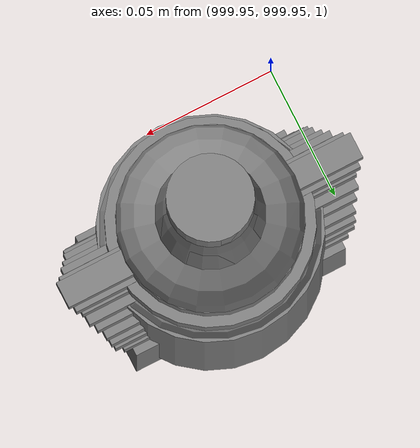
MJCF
<mujoco>
    <option gravity="0.000000000 0.000000000 -9.810000420" timestep="0.0166666" integrator="implicitfast" density="1.225" viscosity="1.8000001e-05" noslip_iterations="10" iterations="100" sdf_iterations="50">
        <flag multiccd="disable"/>
    </option>
    <size memory="1000M"/>
    <compiler coordinate="local"/>
    <worldbody>
        <light cutoff="30" pos="0 1 1" dir="0 -1 -2"/>
        <light cutoff="30" pos="0 -1 1" dir="0 1 -2"/>
        <body pos="-7.168000221 2.823999882 1.227496982" euler="-0.283413976 0.056829724 -0.133293271" name="openloong_gripper_2f85_fix_base_usda_Pos">
            <geom contype="1" conaffinity="1" density="1000" type="box" material="" rgba="0.500000000 0.500000000 0.500000000 1.000000000" solimp="0.899999976 0.949999988 0.001000000" friction="1.000000000 0.005000000 0.000100000" solref="0.020000000 1.000000000" margin="0" condim="3" group="0" pos="-0.002278805 0.074524641 -0.004134059" quat="0.315989345 0.948763072 -0.000000000 0.000000000" size="0.059999999 0.013000000 0.035000000" name="openloong_gripper_2f85_fix_base_usda_geom_F64D209D_FD8C_45CE_AE6E_816473BD5BCD"/>
            <geom contype="1" conaffinity="1" density="1000" type="box" material="" rgba="0.500000000 0.500000000 0.500000000 1.000000000" solimp="0.899999976 0.949999988 0.001000000" friction="1.000000000 0.005000000 0.000100000" solref="0.020000000 1.000000000" margin="0" condim="3" group="0" pos="-0.002278805 0.078031301 0.008128285" quat="0.990447521 -0.137893379 -0.000000000 -0.000000000" size="0.059999999 0.010000000 0.035000000" name="openloong_gripper_2f85_fix_base_usda_geom_AAF5D2DC_7C11_4295_A286_A63D68D4CA72"/>
            <geom contype="1" conaffinity="1" density="1000" type="box" material="" rgba="0.500000000 0.500000000 0.500000000 1.000000000" solimp="0.899999976 0.949999988 0.001000000" friction="1.000000000 0.005000000 0.000100000" solref="0.020000000 1.000000000" margin="0" condim="3" group="0" pos="-0.002278805 0.080785275 -0.002596974" quat="0.287325472 -0.957833409 0.000000000 -0.000000000" size="0.059999999 0.013000000 0.035000000" name="openloong_gripper_2f85_fix_base_usda_geom_FA9A11EE_3D1C_4DF4_8BD6_F97E8DA76BCE"/>
            <geom contype="1" conaffinity="1" density="1000" type="box" material="" rgba="0.500000000 0.500000000 0.500000000 1.000000000" solimp="0.899999976 0.949999988 0.001000000" friction="1.000000000 0.005000000 0.000100000" solref="0.020000000 1.000000000" margin="0" condim="3" group="0" pos="-0.002278805 -0.098804474 -0.020146966" quat="0.988851666 0.148906454 0.000000000 -0.000000000" size="0.059999999 0.022000000 0.020000000" name="openloong_gripper_2f85_fix_base_usda_geom_D758159C_F9BC_4E38_BF4C_C14F445EB0F2"/>
            <geom contype="1" conaffinity="1" density="1000" type="box" material="" rgba="0.500000000 0.500000000 0.500000000 1.000000000" solimp="0.899999976 0.949999988 0.001000000" friction="1.000000000 0.005000000 0.000100000" solref="0.020000000 1.000000000" margin="0" condim="3" group="0" pos="-0.002279282 0.019920111 0.012102962" quat="0.995421767 0.095583342 -0.000000000 -0.000000000" size="0.059999999 0.025000000 0.026000001" name="openloong_gripper_2f85_fix_base_usda_geom_7497A2B2_E80E_404E_BB82_C0E89BF0866C"/>
            <geom contype="1" conaffinity="1" density="1000" type="box" material="" rgba="0.500000000 0.500000000 0.500000000 1.000000000" solimp="0.899999976 0.949999988 0.001000000" friction="1.000000000 0.005000000 0.000100000" solref="0.020000000 1.000000000" margin="0" condim="3" group="0" pos="-0.002279282 0.005734444 -0.014276862" quat="0.999571741 -0.029275302 -0.000000000 -0.000000000" size="0.059999999 0.050000001 0.010000000" name="openloong_gripper_2f85_fix_base_usda_geom_23F4C8E6_5703_4FDB_927C_A1685B983721"/>
            <geom contype="1" conaffinity="1" density="1000" type="box" material="" rgba="0.500000000 0.500000000 0.500000000 1.000000000" solimp="0.899999976 0.949999988 0.001000000" friction="1.000000000 0.005000000 0.000100000" solref="0.020000000 1.000000000" margin="0" condim="3" group="0" pos="-0.002278805 0.079460382 0.007771969" quat="0.922590554 -0.385781586 0.000000000 -0.000000000" size="0.059999999 0.010000000 0.035000000" name="openloong_gripper_2f85_fix_base_usda_geom_FDF5E071_CCFF_4EEF_B0AA_0869B42EF1DD"/>
            <geom contype="1" conaffinity="1" density="1000" type="box" material="" rgba="0.500000000 0.500000000 0.500000000 1.000000000" solimp="0.899999976 0.949999988 0.001000000" friction="1.000000000 0.005000000 0.000100000" solref="0.020000000 1.000000000" margin="0" condim="3" group="0" pos="-0.002279282 0.081384182 -0.001320124" quat="0.590483785 -0.807049930 0.000000000 -0.000000000" size="0.059999999 0.013000000 0.035000000" name="openloong_gripper_2f85_fix_base_usda_geom_FEE93642_7E2A_4812_A104_6F03B24B302F"/>
            <geom contype="1" conaffinity="1" density="1000" type="box" material="" rgba="0.500000000 0.500000000 0.500000000 1.000000000" solimp="0.899999976 0.949999988 0.001000000" friction="1.000000000 0.005000000 0.000100000" solref="0.020000000 1.000000000" margin="0" condim="3" group="0" pos="-0.002278805 -0.059297800 -0.007972836" quat="0.988851666 0.148906454 0.000000000 -0.000000000" size="0.059999999 0.020000000 0.022000000" name="openloong_gripper_2f85_fix_base_usda_geom_18C90464_117E_4221_B8F1_A271FB0B92B5"/>
            <geom contype="1" conaffinity="1" density="1000" type="box" material="" rgba="0.500000000 0.500000000 0.500000000 1.000000000" solimp="0.899999976 0.949999988 0.001000000" friction="1.000000000 0.005000000 0.000100000" solref="0.020000000 1.000000000" margin="0" condim="3" group="0" pos="-0.002278805 0.076618671 -0.004656792" quat="0.004634961 0.999989629 -0.000000000 0.000000000" size="0.059999999 0.013000000 0.035000000" name="openloong_gripper_2f85_fix_base_usda_geom_02B16A76_2D43_4196_B1A0_59833752D17F"/>
            <geom contype="1" conaffinity="1" density="1000" type="box" material="" rgba="0.500000000 0.500000000 0.500000000 1.000000000" solimp="0.899999976 0.949999988 0.001000000" friction="1.000000000 0.005000000 0.000100000" solref="0.020000000 1.000000000" margin="0" condim="3" group="0" pos="-0.002279282 -0.021952629 0.002960086" quat="0.991270423 0.131847665 -0.000000000 0.000000000" size="0.059999999 0.020000000 0.024000000" name="openloong_gripper_2f85_fix_base_usda_geom_CCE7D025_E1C1_4682_BCD3_7D750785C405"/>
            <geom contype="1" conaffinity="1" density="1000" type="box" material="" rgba="0.500000000 0.500000000 0.500000000 1.000000000" solimp="0.899999976 0.949999988 0.001000000" friction="1.000000000 0.005000000 0.000100000" solref="0.020000000 1.000000000" margin="0" condim="3" group="0" pos="-0.002278805 0.081418991 0.002587914" quat="0.803492308 -0.595315695 0.000000000 -0.000000000" size="0.059999999 0.013000000 0.035000000" name="openloong_gripper_2f85_fix_base_usda_geom_2B54C2B7_8CD6_49F2_8CB4_8166ABB43AF3"/>
            <geom contype="1" conaffinity="1" density="1000" type="box" material="" rgba="0.500000000 0.500000000 0.500000000 1.000000000" solimp="0.899999976 0.949999988 0.001000000" friction="1.000000000 0.005000000 0.000100000" solref="0.020000000 1.000000000" margin="0" condim="3" group="0" pos="-0.002278805 0.061115503 0.008545756" quat="0.999326169 0.036714450 0.000000000 -0.000000000" size="0.059999999 0.020000000 0.035000000" name="openloong_gripper_2f85_fix_base_usda_geom_8A2449A8_8873_4208_BE92_FF731361DA6E"/>
            <freejoint name="openloong_gripper_2f85_fix_base_usda_pos_scan"/>
        </body>
        <body pos="-2.198674202 6.274972439 1.695915103" euler="-25.860683441 38.144096375 -28.811243057" mocap="true" name="spotlight5_SpotLight"/>
        <body pos="-2.211471319 6.637242794 1.805454731" euler="46.072456360 1.897168159 22.413496017" mocap="true" name="spotlight6_SpotLight"/>
        <body pos="1000.000000000 1000.000000000 1.000000000" euler="0.000000000 0.000000000 0.000000000" name="openloong_gripper_2f85_fix_base_usda_bottle_red">
            <geom contype="1" conaffinity="1" density="1000" type="ellipsoid" material="" rgba="0.500000000 0.500000000 0.500000000 1.000000000" solimp="0.899999976 0.949999988 0.001000000" friction="1.000000000 0.005000000 0.000100000" solref="0.020000000 1.000000000" margin="0" condim="3" group="0" pos="0.000000000 0.000000000 0.144284487" quat="1.000000000 0.000000000 0.000000000 0.000000000" size="0.021000000 0.021000000 0.079999998" name="openloong_gripper_2f85_fix_base_usda_geom_E1A86D98_7019_4E97_9451_81618C77376A"/>
            <geom contype="1" conaffinity="1" density="1000" type="cylinder" material="" rgba="0.500000000 0.500000000 0.500000000 1.000000000" solimp="0.899999976 0.949999988 0.001000000" friction="1.000000000 0.005000000 0.000100000" solref="0.020000000 1.000000000" margin="0" condim="3" group="0" pos="0.000000000 0.000000000 0.220618963" quat="1.000000000 0.000000000 0.000000000 0.000000000" size="0.016000001 0.010000000 1.000000000" name="openloong_gripper_2f85_fix_base_usda_geom_DD1C388B_7BED_4949_BC3D_ED43878A694D"/>
            <geom contype="1" conaffinity="1" density="1000" type="ellipsoid" material="" rgba="0.500000000 0.500000000 0.500000000 1.000000000" solimp="0.899999976 0.949999988 0.001000000" friction="1.000000000 0.005000000 0.000100000" solref="0.020000000 1.000000000" margin="0" condim="3" group="0" pos="0.000000000 0.000000000 0.118945479" quat="1.000000000 0.000000000 0.000000000 0.000000000" size="0.030999999 0.030999999 0.029999999" name="openloong_gripper_2f85_fix_base_usda_geom_0959E4A8_5653_4632_831B_8B646D143C95"/>
            <geom contype="1" conaffinity="1" density="1000" type="box" material="" rgba="0.500000000 0.500000000 0.500000000 1.000000000" solimp="0.899999976 0.949999988 0.001000000" friction="1.000000000 0.005000000 0.000100000" solref="0.020000000 1.000000000" margin="0" condim="3" group="0" pos="0.000000000 0.000000000 0.002189159" quat="1.000000000 0.000000000 0.000000000 0.000000000" size="0.020000000 0.020000000 0.003000000" name="openloong_gripper_2f85_fix_base_usda_geom_8653921E_4BA2_46D6_96A2_D6CF77724C1E"/>
            <geom contype="1" conaffinity="1" density="1000" type="cylinder" material="" rgba="0.500000000 0.500000000 0.500000000 1.000000000" solimp="0.899999976 0.949999988 0.001000000" friction="1.000000000 0.005000000 0.000100000" solref="0.020000000 1.000000000" margin="0" condim="3" group="0" pos="0.000000000 -0.000366211 0.060884237" quat="1.000000000 0.000000000 0.000000000 0.000000000" size="0.030999999 0.057999998 1.000000000" name="openloong_gripper_2f85_fix_base_usda_geom_39066ED4_C830_4692_99CC_B22A0CBC368C"/>
            <freejoint name="openloong_gripper_2f85_fix_base_usda_bottle_red_joint"/>
            <site size="0.005000000 0.005000000 0.005000000" rgba="0.500000000 0.500000000 0.500000000 1.000000000" pos="0.000000000 0.000000000 0.000000000" quat="0.999961913 0.008726535 0.000000000 0.000000000" group="0" type="sphere" name="openloong_gripper_2f85_fix_base_usda_bottle_redsite"/>
        </body>
        <body pos="-2.203760147 5.861109734 1.769650817" euler="24.091007233 12.925108910 37.792869568" mocap="true" name="spotlight4_SpotLight"/>
        <body pos="1000.000000000 1000.000000000 1.000000000" euler="0.000000000 0.000000000 0.000000000" name="openloong_gripper_2f85_fix_base_usda_can">
            <geom contype="1" conaffinity="1" density="1000" type="cylinder" material="" rgba="0.500000000 0.500000000 0.500000000 1.000000000" solimp="0.899999976 0.949999988 0.001000000" friction="1.000000000 0.005000000 0.000100000" solref="0.020000000 1.000000000" margin="0" condim="3" group="0" pos="0.000000000 0.000000000 0.079676986" quat="1.000000000 0.000000000 0.000000000 0.000000000" size="0.034000002 0.071999997 1.000000000" name="openloong_gripper_2f85_fix_base_usda_geom_9B3FD68F_8CE8_4B49_B60D_CC1B70E38FF8"/>
            <geom contype="1" conaffinity="1" density="1000" type="ellipsoid" material="" rgba="0.500000000 0.500000000 0.500000000 1.000000000" solimp="0.899999976 0.949999988 0.001000000" friction="1.000000000 0.005000000 0.000100000" solref="0.020000000 1.000000000" margin="0" condim="3" group="0" pos="0.000000000 0.000000000 0.151854277" quat="1.000000000 0.000000000 0.000000000 0.000000000" size="0.034000002 0.034000002 0.020000000" name="openloong_gripper_2f85_fix_base_usda_geom_F23DBA2C_55B3_407B_B6FD_89384B69352C"/>
            <geom contype="1" conaffinity="1" density="1000" type="box" material="" rgba="0.500000000 0.500000000 0.500000000 1.000000000" solimp="0.899999976 0.949999988 0.001000000" friction="1.000000000 0.005000000 0.000100000" solref="0.020000000 1.000000000" margin="0" condim="3" group="0" pos="0.000000000 0.000000000 0.004777670" quat="1.000000000 0.000000000 0.000000000 0.000000000" size="0.020000000 0.020000000 0.005000000" name="openloong_gripper_2f85_fix_base_usda_geom_1C0577AF_B7A4_41F4_BC55_D76776C2BE82"/>
            <freejoint name="openloong_gripper_2f85_fix_base_usda_can_joint"/>
            <site size="0.005000000 0.005000000 0.005000000" rgba="0.500000000 0.500000000 0.500000000 1.000000000" pos="0.000000000 0.000000000 0.000000000" quat="1.000000000 0.000000000 0.000000000 0.000000000" group="0" type="sphere" name="openloong_gripper_2f85_fix_base_usda_cansite"/>
        </body>
        <body pos="1000.000000000 1000.000000000 1.000000000" euler="0.000000000 0.000000000 0.000000000" name="openloong_gripper_2f85_fix_base_usda_bottle_blue">
            <geom contype="1" conaffinity="1" density="1000" type="ellipsoid" material="" rgba="0.500000000 0.500000000 0.500000000 1.000000000" solimp="0.899999976 0.949999988 0.001000000" friction="1.000000000 0.005000000 0.000100000" solref="0.020000000 1.000000000" margin="0" condim="3" group="0" pos="0.000000000 0.000000000 0.118920922" quat="1.000000000 0.000000000 0.000000000 0.000000000" size="0.030999999 0.030999999 0.029999999" name="openloong_gripper_2f85_fix_base_usda_geom_C282DF2E_6B78_45E1_A22E_EFE731D1B489"/>
            <geom contype="1" conaffinity="1" density="1000" type="box" material="" rgba="0.500000000 0.500000000 0.500000000 1.000000000" solimp="0.899999976 0.949999988 0.001000000" friction="1.000000000 0.005000000 0.000100000" solref="0.020000000 1.000000000" margin="0" condim="3" group="0" pos="0.000000000 0.000000000 0.002164602" quat="1.000000000 0.000000000 0.000000000 0.000000000" size="0.020000000 0.020000000 0.003000000" name="openloong_gripper_2f85_fix_base_usda_geom_52EB6660_3402_465A_8FF8_93E8D35CA2CB"/>
            <geom contype="1" conaffinity="1" density="1000" type="cylinder" material="" rgba="0.500000000 0.500000000 0.500000000 1.000000000" solimp="0.899999976 0.949999988 0.001000000" friction="1.000000000 0.005000000 0.000100000" solref="0.020000000 1.000000000" margin="0" condim="3" group="0" pos="0.000000000 -0.000366211 0.060859680" quat="1.000000000 0.000000000 0.000000000 0.000000000" size="0.030999999 0.057999998 1.000000000" name="openloong_gripper_2f85_fix_base_usda_geom_E9ED3D49_D7D0_4F8B_A7EC_BF525175AB60"/>
            <geom contype="1" conaffinity="1" density="1000" type="cylinder" material="" rgba="0.500000000 0.500000000 0.500000000 1.000000000" solimp="0.899999976 0.949999988 0.001000000" friction="1.000000000 0.005000000 0.000100000" solref="0.020000000 1.000000000" margin="0" condim="3" group="0" pos="0.000000000 0.000000000 0.220594406" quat="1.000000000 0.000000000 0.000000000 0.000000000" size="0.016000001 0.010000000 1.000000000" name="openloong_gripper_2f85_fix_base_usda_geom_FC434F86_EC70_4646_B3BD_6CE553C9ACF4"/>
            <geom contype="1" conaffinity="1" density="1000" type="ellipsoid" material="" rgba="0.500000000 0.500000000 0.500000000 1.000000000" solimp="0.899999976 0.949999988 0.001000000" friction="1.000000000 0.005000000 0.000100000" solref="0.020000000 1.000000000" margin="0" condim="3" group="0" pos="0.000000000 0.000000000 0.144259930" quat="1.000000000 0.000000000 0.000000000 0.000000000" size="0.021000000 0.021000000 0.079999998" name="openloong_gripper_2f85_fix_base_usda_geom_3A508E19_08D5_478E_9D9E_2A3D620B02E9"/>
            <freejoint name="openloong_gripper_2f85_fix_base_usda_bottle_blue_joint"/>
            <site size="0.005000000 0.005000000 0.005000000" rgba="0.500000000 0.500000000 0.500000000 1.000000000" pos="0.000000000 0.000000000 0.000000000" quat="0.999961913 0.008726535 0.000000000 0.000000000" group="0" type="sphere" name="openloong_gripper_2f85_fix_base_usda_bottle_bluesite"/>
        </body>
        <body pos="1000.000000000 1000.000000000 1.000000000" euler="0.000000000 0.000000000 0.000000000" name="openloong_gripper_2f85_fix_base_usda_salt">
            <geom contype="1" conaffinity="1" density="1000" type="box" material="" rgba="0.500000000 0.500000000 0.500000000 1.000000000" solimp="0.899999976 0.949999988 0.001000000" friction="1.000000000 0.005000000 0.000100000" solref="0.020000000 1.000000000" margin="0" condim="3" group="0" pos="0.000305176 0.000000000 0.084862232" quat="1.000000000 0.000000000 0.000000000 0.000000000" size="0.048999999 0.018999999 0.005000000" name="openloong_gripper_2f85_fix_base_usda_geom_0B7DDB27_DBD8_4F20_B92A_836D750F9851"/>
            <geom contype="1" conaffinity="1" density="1000" type="box" material="" rgba="0.500000000 0.500000000 0.500000000 1.000000000" solimp="0.899999976 0.949999988 0.001000000" friction="1.000000000 0.005000000 0.000100000" solref="0.020000000 1.000000000" margin="0" condim="3" group="0" pos="0.000305176 0.000000000 0.104564309" quat="1.000000000 0.000000000 0.000000000 0.000000000" size="0.052000001 0.014000000 0.005000000" name="openloong_gripper_2f85_fix_base_usda_geom_1176C1DE_5BF1_4690_A503_A0ED4C41B959"/>
            <geom contype="1" conaffinity="1" density="1000" type="box" material="" rgba="0.500000000 0.500000000 0.500000000 1.000000000" solimp="0.899999976 0.949999988 0.001000000" friction="1.000000000 0.005000000 0.000100000" solref="0.020000000 1.000000000" margin="0" condim="3" group="0" pos="0.000305176 0.000000000 0.114487171" quat="1.000000000 0.000000000 0.000000000 0.000000000" size="0.054000001 0.011500000 0.005000000" name="openloong_gripper_2f85_fix_base_usda_geom_DFE59555_A0D9_45DE_8039_0F6A6E0FE68D"/>
            <geom contype="1" conaffinity="1" density="1000" type="box" material="" rgba="0.500000000 0.500000000 0.500000000 1.000000000" solimp="0.899999976 0.949999988 0.001000000" friction="1.000000000 0.005000000 0.000100000" solref="0.020000000 1.000000000" margin="0" condim="3" group="0" pos="0.000305176 0.000000000 0.075103164" quat="1.000000000 0.000000000 0.000000000 0.000000000" size="0.048000000 0.020000000 0.005000000" name="openloong_gripper_2f85_fix_base_usda_geom_E2E484AF_8B43_4571_A962_938A2B1BF7FA"/>
            <geom contype="1" conaffinity="1" density="1000" type="box" material="" rgba="0.500000000 0.500000000 0.500000000 1.000000000" solimp="0.899999976 0.949999988 0.001000000" friction="1.000000000 0.005000000 0.000100000" solref="0.020000000 1.000000000" margin="0" condim="3" group="0" pos="0.000305176 0.000000000 0.134892464" quat="1.000000000 0.000000000 0.000000000 0.000000000" size="0.057000000 0.007000000 0.005000000" name="openloong_gripper_2f85_fix_base_usda_geom_1E092CA8_DDC1_4533_B298_9FADDDE43765"/>
            <geom contype="1" conaffinity="1" density="1000" type="box" material="" rgba="0.500000000 0.500000000 0.500000000 1.000000000" solimp="0.899999976 0.949999988 0.001000000" friction="1.000000000 0.005000000 0.000100000" solref="0.020000000 1.000000000" margin="0" condim="3" group="0" pos="0.000305176 0.000000000 0.094920278" quat="1.000000000 0.000000000 0.000000000 0.000000000" size="0.050000001 0.017000001 0.005000000" name="openloong_gripper_2f85_fix_base_usda_geom_E86EE135_25B5_4A52_8AC6_553D730FA72E"/>
            <geom contype="1" conaffinity="1" density="1000" type="box" material="" rgba="0.500000000 0.500000000 0.500000000 1.000000000" solimp="0.899999976 0.949999988 0.001000000" friction="1.000000000 0.005000000 0.000100000" solref="0.020000000 1.000000000" margin="0" condim="3" group="0" pos="0.000305176 0.000000000 0.065204859" quat="1.000000000 0.000000000 0.000000000 0.000000000" size="0.045000002 0.021000000 0.005000000" name="openloong_gripper_2f85_fix_base_usda_geom_5B723E62_76A4_4EEB_AE70_CCF676BEB054"/>
            <geom contype="1" conaffinity="1" density="1000" type="box" material="" rgba="0.500000000 0.500000000 0.500000000 1.000000000" solimp="0.899999976 0.949999988 0.001000000" friction="1.000000000 0.005000000 0.000100000" solref="0.020000000 1.000000000" margin="0" condim="3" group="0" pos="0.000305176 0.000000000 0.144135714" quat="1.000000000 0.000000000 0.000000000 0.000000000" size="0.059000000 0.005000000 0.004000000" name="openloong_gripper_2f85_fix_base_usda_geom_4272CA67_18A7_4F95_A555_EE959506F338"/>
            <geom contype="1" conaffinity="1" density="1000" type="box" material="" rgba="0.500000000 0.500000000 0.500000000 1.000000000" solimp="0.899999976 0.949999988 0.001000000" friction="1.000000000 0.005000000 0.000100000" solref="0.020000000 1.000000000" margin="0" condim="3" group="0" pos="0.000000000 0.000000000 0.031593561" quat="1.000000000 0.000000000 0.000000000 0.000000000" size="0.041999999 0.024000000 0.029999999" name="openloong_gripper_2f85_fix_base_usda_geom_812F2216_8E10_4FE6_9365_54442E2F67C8"/>
            <geom contype="1" conaffinity="1" density="1000" type="box" material="" rgba="0.500000000 0.500000000 0.500000000 1.000000000" solimp="0.899999976 0.949999988 0.001000000" friction="1.000000000 0.005000000 0.000100000" solref="0.020000000 1.000000000" margin="0" condim="3" group="0" pos="0.000305176 0.000000000 0.124608755" quat="1.000000000 0.000000000 0.000000000 0.000000000" size="0.055000000 0.008000000 0.005000000" name="openloong_gripper_2f85_fix_base_usda_geom_C9F48370_A33B_488A_8648_E361C255127E"/>
            <freejoint name="openloong_gripper_2f85_fix_base_usda_salt_joint"/>
            <site size="0.005000000 0.005000000 0.005000000" rgba="0.500000000 0.500000000 0.500000000 1.000000000" pos="0.000000000 0.000000000 0.000000000" quat="1.000000000 0.000000000 0.000000000 0.000000000" group="0" type="sphere" name="openloong_gripper_2f85_fix_base_usda_saltsite"/>
        </body>
        <body pos="1000.000000000 1000.000000000 1.000000000" euler="0.000000000 0.000000000 0.000000000" name="openloong_gripper_2f85_fix_base_usda_jar_01">
            <geom contype="1" conaffinity="1" density="1000" type="box" material="" rgba="0.500000000 0.500000000 0.500000000 1.000000000" solimp="0.899999976 0.949999988 0.001000000" friction="1.000000000 0.005000000 0.000100000" solref="0.020000000 1.000000000" margin="0" condim="3" group="0" pos="0.000000000 0.000000000 0.006158113" quat="1.000000000 0.000000000 0.000000000 0.000000000" size="0.020000000 0.020000000 0.005000000" name="openloong_gripper_2f85_fix_base_usda_geom_CA5CA242_00DD_4D35_9831_613A824356DF"/>
            <geom contype="1" conaffinity="1" density="1000" type="cylinder" material="" rgba="0.500000000 0.500000000 0.500000000 1.000000000" solimp="0.899999976 0.949999988 0.001000000" friction="1.000000000 0.005000000 0.000100000" solref="0.020000000 1.000000000" margin="0" condim="3" group="0" pos="0.000000000 0.000000000 0.062744498" quat="1.000000000 0.000000000 0.000000000 0.000000000" size="0.041000001 0.052999999 1.000000000" name="openloong_gripper_2f85_fix_base_usda_geom_C714E157_C267_45D0_B1EC_4614613E98CE"/>
            <geom contype="1" conaffinity="1" density="1000" type="ellipsoid" material="" rgba="0.500000000 0.500000000 0.500000000 1.000000000" solimp="0.899999976 0.949999988 0.001000000" friction="1.000000000 0.005000000 0.000100000" solref="0.020000000 1.000000000" margin="0" condim="3" group="0" pos="0.000000000 0.000000000 0.122252703" quat="1.000000000 0.000000000 0.000000000 0.000000000" size="0.035999998 0.035999998 0.010000000" name="openloong_gripper_2f85_fix_base_usda_geom_905B33BB_3F97_482E_8F45_A6ADAD1F279F"/>
            <geom contype="1" conaffinity="1" density="1000" type="cylinder" material="" rgba="0.500000000 0.500000000 0.500000000 1.000000000" solimp="0.899999976 0.949999988 0.001000000" friction="1.000000000 0.005000000 0.000100000" solref="0.020000000 1.000000000" margin="0" condim="3" group="0" pos="0.000000000 0.000000000 0.015747190" quat="1.000000000 0.000000000 0.000000000 0.000000000" size="0.035000000 0.010000000 1.000000000" name="openloong_gripper_2f85_fix_base_usda_geom_D13A1273_583F_4113_948A_69F6F8D78D29"/>
            <geom contype="1" conaffinity="1" density="1000" type="ellipsoid" material="" rgba="0.500000000 0.500000000 0.500000000 1.000000000" solimp="0.899999976 0.949999988 0.001000000" friction="1.000000000 0.005000000 0.000100000" solref="0.020000000 1.000000000" margin="0" condim="3" group="0" pos="0.000000000 0.000000000 0.115815401" quat="1.000000000 0.000000000 0.000000000 0.000000000" size="0.039999999 0.039999999 0.010000000" name="openloong_gripper_2f85_fix_base_usda_geom_E6533F1D_7DC3_4CD9_9652_73757B9FA6CD"/>
            <geom contype="1" conaffinity="1" density="1000" type="cylinder" material="" rgba="0.500000000 0.500000000 0.500000000 1.000000000" solimp="0.899999976 0.949999988 0.001000000" friction="1.000000000 0.005000000 0.000100000" solref="0.020000000 1.000000000" margin="0" condim="3" group="0" pos="0.000000000 0.000000000 0.133183479" quat="1.000000000 0.000000000 0.000000000 0.000000000" size="0.037999999 0.006500000 1.000000000" name="openloong_gripper_2f85_fix_base_usda_geom_A2EF223C_7F68_44CF_9DB2_35483C24BA87"/>
            <freejoint name="openloong_gripper_2f85_fix_base_usda_jar_01_joint"/>
            <site size="0.005000000 0.005000000 0.005000000" rgba="0.500000000 0.500000000 0.500000000 1.000000000" pos="0.000000000 0.000000000 0.000000000" quat="1.000000000 0.000000000 0.000000000 0.000000000" group="0" type="sphere" name="openloong_gripper_2f85_fix_base_usda_jar_01site"/>
        </body>
        <body pos="0.000000000 0.000000000 0.000000000" euler="0.000000000 0.000000000 0.000000000" name="Interactive Objects_Interactive Objects"/>
        <body pos="0.000000000 0.000000000 0.000000000" euler="0.000000000 0.000000000 0.000000000" name=" Static Objects_ Static Objects">
            <geom contype="1" conaffinity="1" density="1000" type="box" material="" rgba="0.500000000 0.500000000 0.500000000 1.000000000" solimp="0.899999976 0.949999988 0.001000000" friction="1.000000000 0.005000000 0.000100000" solref="0.020000000 1.000000000" margin="0" condim="3" group="0" pos="-6.286010742 6.153595448 1.563861728" quat="0.707107067 0.000000000 0.000000000 0.707106471" size="0.529999971 3.134999990 0.025000000" name=" Static Objects_geom_E6FB0B5A_20BF_4A1C_A764_0E7E9A3B27D7"/>
            <geom contype="1" conaffinity="1" density="1000" type="box" material="" rgba="0.500000000 0.500000000 0.500000000 1.000000000" solimp="0.899999976 0.949999988 0.001000000" friction="1.000000000 0.005000000 0.000100000" solref="0.020000000 1.000000000" margin="0" condim="3" group="0" pos="-3.101639986 6.150595188 1.018643856" quat="1.000000000 0.000000000 0.000000000 0.000000000" size="0.050000001 0.579999983 1.019999981" name=" Static Objects_geom_9EA61F48_DF7A_4D75_9151_AC47522CC19C"/>
            <geom contype="1" conaffinity="1" density="1000" type="box" material="" rgba="0.500000000 0.500000000 0.500000000 1.000000000" solimp="0.899999976 0.949999988 0.001000000" friction="1.000000000 0.005000000 0.000100000" solref="0.020000000 1.000000000" margin="0" condim="3" group="0" pos="-2.825197220 6.153595448 1.563861728" quat="0.707107067 0.000000000 0.000000000 0.707106471" size="0.550000012 0.239999995 0.025000000" name=" Static Objects_geom_78E1BBFF_1921_4675_BA05_E71DB2258D7C"/>
            <geom contype="1" conaffinity="1" density="1000" type="box" material="" rgba="0.500000000 0.500000000 0.500000000 1.000000000" solimp="0.899999976 0.949999988 0.001000000" friction="1.000000000 0.005000000 0.000100000" solref="0.020000000 1.000000000" margin="0" condim="3" group="0" pos="-6.311686516 6.153595448 1.018643856" quat="0.707107067 0.000000000 0.000000000 0.707106471" size="0.050000001 3.150000095 1.019999981" name=" Static Objects_geom_6A4F16FE_3FAA_4001_8756_D084555F2924"/>
            <geom contype="1" conaffinity="1" density="1000" type="box" material="" rgba="0.500000000 0.500000000 0.500000000 1.000000000" solimp="0.899999976 0.949999988 0.001000000" friction="1.000000000 0.005000000 0.000100000" solref="0.020000000 1.000000000" margin="0" condim="3" group="0" pos="-2.825197220 6.153595448 1.115278244" quat="0.707107067 0.000000000 0.000000000 0.707106471" size="0.550000012 0.239999995 0.025000000" name=" Static Objects_geom_D805BB58_5F57_4738_A1DA_3FC8BEA04025"/>
            <geom contype="1" conaffinity="1" density="1000" type="box" material="" rgba="0.500000000 0.500000000 0.500000000 1.000000000" solimp="0.899999976 0.949999988 0.001000000" friction="1.000000000 0.005000000 0.000100000" solref="0.020000000 1.000000000" margin="0" condim="3" group="0" pos="-6.293097973 6.153595448 1.114443064" quat="0.707107067 0.000000000 0.000000000 0.707106471" size="0.529999971 3.134999990 0.025000000" name=" Static Objects_geom_DCD387C7_D713_49A7_8928_DB1EB11B60DC"/>
            <geom contype="1" conaffinity="1" density="1000" type="box" material="" rgba="0.500000000 0.500000000 0.500000000 1.000000000" solimp="0.899999976 0.949999988 0.001000000" friction="1.000000000 0.005000000 0.000100000" solref="0.020000000 1.000000000" margin="0" condim="3" group="0" pos="-2.825197220 6.153595448 0.629031777" quat="0.707107067 0.000000000 0.000000000 0.707106471" size="0.550000012 0.239999995 0.025000000" name=" Static Objects_geom_3E0EE0AA_56F3_4B04_A345_2DA36F0C352F"/>
            <geom contype="1" conaffinity="1" density="1000" type="box" material="" rgba="0.500000000 0.500000000 0.500000000 1.000000000" solimp="0.899999976 0.949999988 0.001000000" friction="1.000000000 0.005000000 0.000100000" solref="0.020000000 1.000000000" margin="0" condim="3" group="0" pos="-6.286010742 6.153595448 0.096129179" quat="0.707107067 0.000000000 0.000000000 0.707106471" size="0.529999971 3.134999990 0.098999999" name=" Static Objects_geom_41234DC5_D7DB_4324_B5F9_7E1C62A07A3D"/>
            <geom contype="1" conaffinity="1" density="1000" type="box" material="" rgba="0.500000000 0.500000000 0.500000000 1.000000000" solimp="0.899999976 0.949999988 0.001000000" friction="1.000000000 0.005000000 0.000100000" solref="0.020000000 1.000000000" margin="0" condim="3" group="0" pos="-2.825197220 6.153595448 0.097434282" quat="0.707107067 0.000000000 0.000000000 0.707106471" size="0.550000012 0.239999995 0.098999999" name=" Static Objects_geom_8EF30A8D_E099_4062_B098_7F13DEDA207B"/>
            <geom contype="1" conaffinity="1" density="1000" type="box" material="" rgba="0.500000000 0.500000000 0.500000000 1.000000000" solimp="0.899999976 0.949999988 0.001000000" friction="1.000000000 0.005000000 0.000100000" solref="0.020000000 1.000000000" margin="0" condim="3" group="0" pos="-6.286010742 6.153595448 0.629031777" quat="0.707107067 0.000000000 0.000000000 0.707106471" size="0.529999971 3.134999990 0.025000000" name=" Static Objects_geom_E7E4BBD1_28BF_47DB_9284_735186979730"/>
            <geom contype="1" conaffinity="1" density="1000" type="box" material="" rgba="0.500000000 0.500000000 0.500000000 1.000000000" solimp="0.899999976 0.949999988 0.001000000" friction="1.000000000 0.005000000 0.000100000" solref="0.020000000 1.000000000" margin="0" condim="3" group="0" pos="-6.000000000 20.159999847 2.000000000" quat="1.000000000 0.000000000 0.000000000 0.000000000" size="6.079999924 0.070000000 2.000000000" name=" Static Objects_geom_4F2F79EB_1C62_4B3A_9C0A_A9693456D2AC"/>
            <geom contype="1" conaffinity="1" density="1000" type="box" material="" rgba="0.500000000 0.500000000 0.500000000 1.000000000" solimp="0.899999976 0.949999988 0.001000000" friction="1.000000000 0.005000000 0.000100000" solref="0.020000000 1.000000000" margin="0" condim="3" group="0" pos="-6.000000000 0.035000000 2.000000000" quat="1.000000000 0.000000000 0.000000000 0.000000000" size="6.079999924 0.070000000 2.000000000" name=" Static Objects_geom_4620CAA1_EC26_47FD_83D8_42B4D4D508E8"/>
            <geom contype="1" conaffinity="1" density="1000" type="box" material="" rgba="0.500000000 0.500000000 0.500000000 1.000000000" solimp="0.899999976 0.949999988 0.001000000" friction="1.000000000 0.005000000 0.000100000" solref="0.020000000 1.000000000" margin="0" condim="3" group="0" pos="0.000000000 10.000000000 2.000000000" quat="1.000000000 0.000000000 0.000000000 0.000000000" size="0.070000000 10.500000000 2.000000000" name=" Static Objects_geom_79A65BCA_E619_4F99_9859_020BDF033FF8"/>
            <geom contype="1" conaffinity="1" density="1000" type="box" material="" rgba="0.500000000 0.500000000 0.500000000 1.000000000" solimp="0.899999976 0.949999988 0.001000000" friction="1.000000000 0.005000000 0.000100000" solref="0.020000000 1.000000000" margin="0" condim="3" group="0" pos="-12.050000191 10.000000000 2.000000000" quat="1.000000000 0.000000000 0.000000000 0.000000000" size="0.070000000 10.500000000 2.000000000" name=" Static Objects_geom_089D2730_3215_4167_A80D_09799544FBDB"/>
            <geom contype="1" conaffinity="1" density="1000" type="plane" material="" rgba="0.500000000 0.500000000 0.500000000 1.000000000" solimp="0.899999976 0.949999988 0.001000000" friction="1.000000000 0.005000000 0.000100000" solref="0.020000000 1.000000000" margin="0" condim="3" group="0" pos="-6.000000000 10.399999619 0.000000000" quat="1.000000000 0.000000000 0.000000000 0.000000000" size="6.050000191 10.800000191 0.010000000" name=" Static Objects_geom_88C9CFEE_19E3_4D68_A5B0_121B475C9200"/>
            <geom contype="1" conaffinity="1" density="1000" type="box" material="" rgba="0.500000000 0.500000000 0.500000000 1.000000000" solimp="0.899999976 0.949999988 0.001000000" friction="1.000000000 0.005000000 0.000100000" solref="0.020000000 1.000000000" margin="0" condim="3" group="0" pos="-8.830721855 2.096410990 0.549305558" quat="1.000000000 0.000000000 0.000000000 0.000000000" size="0.280000001 0.430000007 0.550000012" name=" Static Objects_geom_F9156619_3090_41D7_867F_5EBBB5ADCBD2"/>
            <geom contype="1" conaffinity="1" density="1000" type="box" material="" rgba="0.500000000 0.500000000 0.500000000 1.000000000" solimp="0.899999976 0.949999988 0.001000000" friction="1.000000000 0.005000000 0.000100000" solref="0.020000000 1.000000000" margin="0" condim="3" group="0" pos="-6.460197449 2.937205315 0.548931718" quat="1.000000000 0.000000000 0.000000000 0.000000000" size="2.650000095 0.430000007 0.550000012" name=" Static Objects_geom_BD6BE898_DE86_4418_894E_68F4AC85E5F5"/>
            <geom contype="1" conaffinity="1" density="1000" type="box" material="" rgba="0.500000000 0.500000000 0.500000000 1.000000000" solimp="0.899999976 0.949999988 0.001000000" friction="1.000000000 0.005000000 0.000100000" solref="0.020000000 1.000000000" margin="0" condim="3" group="0" pos="-4.240264893 1.327049494 0.549888909" quat="1.000000000 0.000000000 0.000000000 0.000000000" size="0.430000007 1.200000048 0.550000012" name=" Static Objects_geom_0A4B6D39_A378_4E9A_827D_B5684852B0EB"/>
            <geom contype="1" conaffinity="1" density="1000" type="box" material="" rgba="0.500000000 0.500000000 0.500000000 1.000000000" solimp="0.899999976 0.949999988 0.001000000" friction="1.000000000 0.005000000 0.000100000" solref="0.020000000 1.000000000" margin="0" condim="3" group="0" pos="-7.408766270 3.088089943 1.776644945" quat="0.928051054 0.000000000 0.000000000 0.372453064" size="0.050000001 0.100000001 0.050000001" name=" Static Objects_geom_D432ABDF_2915_43D5_BE4E_FA829D295F97"/>
            <geom contype="1" conaffinity="1" density="1000" type="box" material="" rgba="0.500000000 0.500000000 0.500000000 1.000000000" solimp="0.899999976 0.949999988 0.001000000" friction="1.000000000 0.005000000 0.000100000" solref="0.020000000 1.000000000" margin="0" condim="3" group="0" pos="-7.437745571 3.067511320 1.289965630" quat="1.000000000 0.000000000 0.000000000 0.000000000" size="0.029999999 0.020000000 0.020000000" name=" Static Objects_geom_75B7F57B_FAA4_4F68_90E7_107BD97B5C7F"/>
            <geom contype="1" conaffinity="1" density="1000" type="box" material="" rgba="0.500000000 0.500000000 0.500000000 1.000000000" solimp="0.899999976 0.949999988 0.001000000" friction="1.000000000 0.005000000 0.000100000" solref="0.020000000 1.000000000" margin="0" condim="3" group="0" pos="-7.719123363 2.867671013 1.173410416" quat="1.000000000 0.000000000 0.000000000 0.000000000" size="0.250000000 0.250000000 0.079999998" name=" Static Objects_geom_5005F0F8_C907_4188_B10E_D9C823138817"/>
            <geom contype="1" conaffinity="1" density="1000" type="box" material="" rgba="0.500000000 0.500000000 0.500000000 1.000000000" solimp="0.899999976 0.949999988 0.001000000" friction="1.000000000 0.005000000 0.000100000" solref="0.020000000 1.000000000" margin="0" condim="3" group="0" pos="-7.719123363 2.958004713 1.530241251" quat="1.000000000 0.000000000 0.000000000 0.000000000" size="0.250000000 0.159999996 0.280000001" name=" Static Objects_geom_91E03C65_CEC7_4D1F_B0F7_C0CEE25093EB"/>
            <geom contype="1" conaffinity="1" density="1000" type="cylinder" material="" rgba="0.500000000 0.500000000 0.500000000 1.000000000" solimp="0.899999976 0.949999988 0.001000000" friction="1.000000000 0.005000000 0.000100000" solref="0.020000000 1.000000000" margin="0" condim="3" group="0" pos="-7.427312374 3.069516420 1.502544641" quat="0.928051054 0.000000000 0.000000000 0.372453064" size="0.015000000 0.230000004 0.100000001" name=" Static Objects_geom_ADD98A0A_A9E5_4C86_9B0B_9538C0A76FE8"/>
            <geom contype="1" conaffinity="1" density="1000" type="box" material="" rgba="0.500000000 0.500000000 0.500000000 1.000000000" solimp="0.899999976 0.949999988 0.001000000" friction="1.000000000 0.005000000 0.000100000" solref="0.020000000 1.000000000" margin="0" condim="3" group="0" pos="-9.058088303 6.434794426 1.209077358" quat="1.000000000 0.000000000 0.000000000 0.000000000" size="0.250000000 0.100000001 0.070000000" name=" Static Objects_geom_B485A436_F52F_4F3A_9B8E_BC74A341D44E"/>
            <geom contype="1" conaffinity="1" density="1000" type="box" material="" rgba="0.500000000 0.500000000 0.500000000 1.000000000" solimp="0.899999976 0.949999988 0.001000000" friction="1.000000000 0.005000000 0.000100000" solref="0.020000000 1.000000000" margin="0" condim="3" group="0" pos="-5.611940861 6.318420410 0.350975692" quat="1.000000000 0.000000000 0.000000000 0.000000000" size="0.699999988 0.100000001 0.150000006" name=" Static Objects_geom_364C750D_5F09_4C5B_B3B3_650D06EE2A0D"/>
            <geom contype="1" conaffinity="1" density="1000" type="box" material="" rgba="0.500000000 0.500000000 0.500000000 1.000000000" solimp="0.899999976 0.949999988 0.001000000" friction="1.000000000 0.005000000 0.000100000" solref="0.020000000 1.000000000" margin="0" condim="3" group="0" pos="-9.237723351 6.464855671 1.209077358" quat="1.000000000 0.000000000 0.000000000 0.000000000" size="0.100000001 0.100000001 0.070000000" name=" Static Objects_geom_85F50B73_005B_473C_BA55_A3EA20C82916"/>
            <geom contype="1" conaffinity="1" density="1000" type="box" material="" rgba="0.500000000 0.500000000 0.500000000 1.000000000" solimp="0.899999976 0.949999988 0.001000000" friction="1.000000000 0.005000000 0.000100000" solref="0.020000000 1.000000000" margin="0" condim="3" group="0" pos="-6.300771236 6.459744930 1.744376063" quat="1.000000000 0.000000000 0.000000000 0.000000000" size="3.000000000 0.200000003 0.150000006" name=" Static Objects_geom_C4776929_8E38_409E_824A_6D4EFFBE93C3"/>
            <geom contype="1" conaffinity="1" density="1000" type="box" material="" rgba="0.500000000 0.500000000 0.500000000 1.000000000" solimp="0.899999976 0.949999988 0.001000000" friction="1.000000000 0.005000000 0.000100000" solref="0.020000000 1.000000000" margin="0" condim="3" group="0" pos="-7.373087406 6.458900928 1.214329123" quat="1.000000000 0.000000000 0.000000000 0.000000000" size="0.250000000 0.200000003 0.075000003" name=" Static Objects_geom_6AEAF49A_8187_45CC_ACE0_65C0F0A93CBD"/>
            <geom contype="1" conaffinity="1" density="1000" type="box" material="" rgba="0.500000000 0.500000000 0.500000000 1.000000000" solimp="0.899999976 0.949999988 0.001000000" friction="1.000000000 0.005000000 0.000100000" solref="0.020000000 1.000000000" margin="0" condim="3" group="0" pos="-4.035642624 6.459744930 0.352518857" quat="1.000000000 0.000000000 0.000000000 0.000000000" size="0.800000012 0.200000003 0.150000006" name=" Static Objects_geom_40B0C8FC_69E9_47D0_8CFF_E510721D5523"/>
            <geom contype="1" conaffinity="1" density="1000" type="box" material="" rgba="0.500000000 0.500000000 0.500000000 1.000000000" solimp="0.899999976 0.949999988 0.001000000" friction="1.000000000 0.005000000 0.000100000" solref="0.020000000 1.000000000" margin="0" condim="3" group="0" pos="-3.907610416 6.318625927 0.800981164" quat="1.000000000 0.000000000 0.000000000 0.000000000" size="0.500000000 0.100000001 0.150000006" name=" Static Objects_geom_D3798C39_2651_47C5_A976_DFBFB70BBC9F"/>
            <geom contype="1" conaffinity="1" density="1000" type="box" material="" rgba="0.500000000 0.500000000 0.500000000 1.000000000" solimp="0.899999976 0.949999988 0.001000000" friction="1.000000000 0.005000000 0.000100000" solref="0.020000000 1.000000000" margin="0" condim="3" group="0" pos="-6.098561764 6.327973843 1.292199373" quat="1.000000000 0.000000000 0.000000000 0.000000000" size="0.500000000 0.100000001 0.150000006" name=" Static Objects_geom_07DBB0E2_5F9E_4618_804E_36AA9AE5C069"/>
            <geom contype="1" conaffinity="1" density="1000" type="box" material="" rgba="0.500000000 0.500000000 0.500000000 1.000000000" solimp="0.899999976 0.949999988 0.001000000" friction="1.000000000 0.005000000 0.000100000" solref="0.020000000 1.000000000" margin="0" condim="3" group="0" pos="-7.886891365 6.459744930 0.352518857" quat="1.000000000 0.000000000 0.000000000 0.000000000" size="1.500000000 0.200000003 0.150000006" name=" Static Objects_geom_70209427_207F_4BE4_958B_A217D1426BF3"/>
            <geom contype="1" conaffinity="1" density="1000" type="box" material="" rgba="0.500000000 0.500000000 0.500000000 1.000000000" solimp="0.899999976 0.949999988 0.001000000" friction="1.000000000 0.005000000 0.000100000" solref="0.020000000 1.000000000" margin="0" condim="3" group="0" pos="-6.824534416 6.447464466 1.212718010" quat="1.000000000 0.000000000 0.000000000 0.000000000" size="0.100000001 0.100000001 0.075000003" name=" Static Objects_geom_5FD50E39_5DD0_4349_8308_02997A0F6343"/>
            <geom contype="1" conaffinity="1" density="1000" type="box" material="" rgba="0.500000000 0.500000000 0.500000000 1.000000000" solimp="0.899999976 0.949999988 0.001000000" friction="1.000000000 0.005000000 0.000100000" solref="0.020000000 1.000000000" margin="0" condim="3" group="0" pos="-4.407354832 6.459744930 1.292199373" quat="1.000000000 0.000000000 0.000000000 0.000000000" size="1.240000010 0.200000003 0.150000006" name=" Static Objects_geom_883743BD_EC7C_40CD_83E3_CE8EE976E311"/>
            <geom contype="1" conaffinity="1" density="1000" type="box" material="" rgba="0.500000000 0.500000000 0.500000000 1.000000000" solimp="0.899999976 0.949999988 0.001000000" friction="1.000000000 0.005000000 0.000100000" solref="0.020000000 1.000000000" margin="0" condim="3" group="0" pos="-6.751636982 6.459744930 0.800981164" quat="1.000000000 0.000000000 0.000000000 0.000000000" size="2.200000048 0.200000003 0.150000006" name=" Static Objects_geom_F5CB4437_3E42_4C0B_869F_4FFD73FB20A9"/>
            <geom contype="1" conaffinity="1" density="1000" type="box" material="" rgba="0.500000000 0.500000000 0.500000000 1.000000000" solimp="0.899999976 0.949999988 0.001000000" friction="1.000000000 0.005000000 0.000100000" solref="0.020000000 1.000000000" margin="0" condim="3" group="0" pos="-6.924745083 6.362090111 1.214329123" quat="1.000000000 0.000000000 0.000000000 0.000000000" size="0.200000003 0.100000001 0.075000003" name=" Static Objects_geom_BDB0359E_EE8F_422D_9217_E92FDB931768"/>
            <geom contype="1" conaffinity="1" density="1000" type="box" material="" rgba="0.500000000 0.500000000 0.500000000 1.000000000" solimp="0.899999976 0.949999988 0.001000000" friction="1.000000000 0.005000000 0.000100000" solref="0.020000000 1.000000000" margin="0" condim="3" group="0" pos="-8.844120979 6.464855671 1.209077358" quat="1.000000000 0.000000000 0.000000000 0.000000000" size="0.100000001 0.100000001 0.070000000" name=" Static Objects_geom_89EA90D2_F2C8_42EC_9F84_4D8B1B51C3C3"/>
            <geom contype="1" conaffinity="1" density="1000" type="box" material="" rgba="0.500000000 0.500000000 0.500000000 1.000000000" solimp="0.899999976 0.949999988 0.001000000" friction="1.000000000 0.005000000 0.000100000" solref="0.020000000 1.000000000" margin="0" condim="3" group="0" pos="-3.157672644 6.136868477 1.348373055" quat="1.000000000 0.000000000 0.000000000 0.000000000" size="0.200000003 0.519999981 0.300000012" name=" Static Objects_geom_0FF4E5A2_D3A0_4AB3_B61C_90A5766E6D46"/>
        </body>
        <body pos="-6.332345009 2.779978037 1.034067392" euler="0.000000000 0.000000000 0.000000000" name="openloong_gripper_2f85_fix_base_usda_basket">
            <geom contype="1" conaffinity="1" density="100000" type="box" material="" rgba="0.500000000 0.500000000 0.500000000 1.000000000" solimp="0.899999976 0.949999988 0.001000000" friction="1.000000000 0.899999976 0.000100000" solref="0.020000000 1.000000000" margin="0" condim="3" group="0" pos="-0.039724827 -0.188568115 0.167089701" quat="0.997537494 0.070135131 0.000000000 0.000000000" size="0.150000006 0.006000000 0.108000003" name="openloong_gripper_2f85_fix_base_usda_geom_3950042A_12EC_4176_B8E6_6AE4332082AA"/>
            <geom contype="1" conaffinity="1" density="100000" type="box" material="" rgba="0.500000000 0.500000000 0.500000000 1.000000000" solimp="0.899999976 0.949999988 0.001000000" friction="1.000000000 0.899999976 0.000100000" solref="0.020000000 1.000000000" margin="0" condim="3" group="0" pos="0.094372749 0.000000000 0.168361664" quat="0.706172049 0.036353335 0.036353379 0.706171215" size="0.200000003 0.006000000 0.108000003" name="openloong_gripper_2f85_fix_base_usda_geom_CDEE831D_F750_4985_A980_5C70315FEA36"/>
            <geom contype="1" conaffinity="1" density="100000" type="box" material="" rgba="0.500000000 0.500000000 0.500000000 1.000000000" solimp="0.899999976 0.949999988 0.001000000" friction="1.000000000 0.899999976 0.000100000" solref="0.020000000 1.000000000" margin="0" condim="3" group="0" pos="-0.039724827 0.000000000 0.068126202" quat="1.000000000 0.000000000 0.000000000 0.000000000" size="0.129999995 0.174999997 0.006000000" name="openloong_gripper_2f85_fix_base_usda_geom_3812A159_FE99_4EFF_ACFC_59011D896DB3"/>
            <geom contype="1" conaffinity="1" density="100000" type="box" material="" rgba="0.500000000 0.500000000 0.500000000 1.000000000" solimp="0.899999976 0.949999988 0.001000000" friction="1.000000000 0.899999976 0.000100000" solref="0.020000000 1.000000000" margin="0" condim="3" group="0" pos="-0.039724827 0.188377380 0.167089701" quat="0.997489929 -0.070808925 0.000000000 0.000000000" size="0.150000006 0.006000000 0.108000003" name="openloong_gripper_2f85_fix_base_usda_geom_CE89D64A_34C9_4041_AD68_20E440355FEA"/>
            <geom contype="1" conaffinity="1" density="100000" type="box" material="" rgba="0.500000000 0.500000000 0.500000000 1.000000000" solimp="0.899999976 0.949999988 0.001000000" friction="1.000000000 0.899999976 0.000100000" solref="0.020000000 1.000000000" margin="0" condim="3" group="0" pos="-0.172339439 0.000000000 0.168361664" quat="0.706172407 -0.036353018 -0.036353093 0.706170976" size="0.200000003 0.006000000 0.108000003" name="openloong_gripper_2f85_fix_base_usda_geom_7823A5CE_A173_4B2E_AED6_BC80999833D3"/>
            <freejoint name="openloong_gripper_2f85_fix_base_usda_basket_joint"/>
            <site size="0.005000000 0.005000000 0.005000000" rgba="0.500000000 0.500000000 0.500000000 1.000000000" pos="0.000000000 0.000000000 0.000000000" quat="1.000000000 0.000000000 0.000000000 0.000000000" group="0" type="sphere" name="openloong_gripper_2f85_fix_base_usda_basketsite"/>
        </body>
        <body pos="-3.510578632 3.403555870 -0.000000100" euler="0.000000000 0.000000000 40.200675964" name="openloong_gripper_2f85_fix_base_usda_PZ">
            <geom contype="1" conaffinity="1" density="1000" type="box" material="" rgba="0.500000000 0.500000000 0.500000000 1.000000000" solimp="0.899999976 0.949999988 0.001000000" friction="1.000000000 0.005000000 0.000100000" solref="0.020000000 1.000000000" margin="0" condim="3" group="0" pos="-0.047453165 0.056484699 0.373715430" quat="0.934750080 0.077914521 0.028795123 0.345459938" size="0.180000007 0.010000000 0.379999995" name="openloong_gripper_2f85_fix_base_usda_geom_56EB568F_21C8_4FE1_AB1E_406AC43C7D0C"/>
            <geom contype="1" conaffinity="1" density="1000" type="box" material="" rgba="0.500000000 0.500000000 0.500000000 1.000000000" solimp="0.899999976 0.949999988 0.001000000" friction="1.000000000 0.005000000 0.000100000" solref="0.020000000 1.000000000" margin="0" condim="3" group="0" pos="0.047452450 -0.054376602 0.374072611" quat="0.934387863 -0.082143910 -0.030358355 0.345326364" size="0.180000007 0.010000000 0.379999995" name="openloong_gripper_2f85_fix_base_usda_geom_AD45737B_F411_46E3_9993_8780C592636D"/>
            <freejoint name="openloong_gripper_2f85_fix_base_usda_PZ"/>
        </body>
        <body pos="-2.436573029 6.404376507 0.137849092" euler="0.000000000 0.000000000 0.000000000" name="openloong_gripper_2f85_fix_base_usda_shoppingtrolley_01">
            <geom contype="1" conaffinity="1" density="1000" type="box" material="" rgba="0.500000000 0.500000000 0.500000000 1.000000000" solimp="0.899999976 0.949999988 0.001000000" friction="1.000000000 0.005000000 0.000100000" solref="0.020000000 1.000000000" margin="0" condim="3" group="0" pos="-0.107458733 0.238907143 0.911498845" quat="0.634576976 0.622505128 -0.330067992 -0.317575932" size="0.017999999 0.022499999 0.035999998" name="openloong_gripper_2f85_fix_base_usda_geom_20AC6663_D1A8_4BC5_9411_5C82F1C6C6FD"/>
            <geom contype="1" conaffinity="1" density="1000" type="box" material="" rgba="0.500000000 0.500000000 0.500000000 1.000000000" solimp="0.899999976 0.949999988 0.001000000" friction="1.000000000 0.005000000 0.000100000" solref="0.020000000 1.000000000" margin="0" condim="3" group="0" pos="-0.126757339 -0.182533979 0.598989725" quat="0.996607184 0.055331606 -0.059003651 -0.015205891" size="0.013499999 0.287999988 0.053999998" name="openloong_gripper_2f85_fix_base_usda_geom_9B16EE55_1A49_4701_9D84_99EC75B699FB"/>
            <geom contype="1" conaffinity="1" density="1000" type="box" material="" rgba="0.500000000 0.500000000 0.500000000 1.000000000" solimp="0.899999976 0.949999988 0.001000000" friction="1.000000000 0.005000000 0.000100000" solref="0.020000000 1.000000000" margin="0" condim="3" group="0" pos="-0.005004787 0.248085022 0.912686050" quat="1.000000000 0.000000000 0.000000000 0.000000000" size="0.107999995 0.022499999 0.022499999" name="openloong_gripper_2f85_fix_base_usda_geom_C4953756_BC8E_4E5E_A6AB_E0CC193C0EB5"/>
            <geom contype="1" conaffinity="1" density="1000" type="box" material="" rgba="0.500000000 0.500000000 0.500000000 1.000000000" solimp="0.899999976 0.949999988 0.001000000" friction="1.000000000 0.005000000 0.000100000" solref="0.020000000 1.000000000" margin="0" condim="3" group="0" pos="-0.169898406 -0.043119621 0.915120542" quat="0.687021017 0.726584017 -0.005590606 -0.006832919" size="0.017999999 0.022499999 0.089999996" name="openloong_gripper_2f85_fix_base_usda_geom_D1144DE6_5D9B_49D5_BAC5_78A2925B1B8A"/>
            <geom contype="1" conaffinity="1" density="1000" type="box" material="" rgba="0.500000000 0.500000000 0.500000000 1.000000000" solimp="0.899999976 0.949999988 0.001000000" friction="1.000000000 0.005000000 0.000100000" solref="0.020000000 1.000000000" margin="0" condim="3" group="0" pos="0.148195267 -0.199506566 0.782808602" quat="0.998808920 0.017156634 0.026950166 0.036880098" size="0.013499999 0.305999994 0.063000001" name="openloong_gripper_2f85_fix_base_usda_geom_E3E51C3C_1887_4A04_91E4_A6B373380077"/>
            <geom contype="1" conaffinity="1" density="1000" type="box" material="" rgba="0.500000000 0.500000000 0.500000000 1.000000000" solimp="0.899999976 0.949999988 0.001000000" friction="1.000000000 0.005000000 0.000100000" solref="0.020000000 1.000000000" margin="0" condim="3" group="0" pos="-0.142927840 -0.199506134 0.784674108" quat="0.998421252 0.016904408 -0.027109101 -0.046199299" size="0.013499999 0.305999994 0.063000001" name="openloong_gripper_2f85_fix_base_usda_geom_2BA85455_25A1_43F9_BA04_263B754171DB"/>
            <geom contype="1" conaffinity="1" density="1000" type="box" material="" rgba="0.500000000 0.500000000 0.500000000 1.000000000" solimp="0.899999976 0.949999988 0.001000000" friction="1.000000000 0.005000000 0.000100000" solref="0.020000000 1.000000000" margin="0" condim="3" group="0" pos="-0.000004721 -0.174527690 0.560063601" quat="0.996704638 0.081116498 -0.000000004 0.000000000" size="0.126000002 0.287999988 0.009000000" name="openloong_gripper_2f85_fix_base_usda_geom_73DA0DDD_91FE_4031_8C30_C3BC3B7BAD4C"/>
            <geom contype="1" conaffinity="1" density="1000" type="box" material="" rgba="0.500000000 0.500000000 0.500000000 1.000000000" solimp="0.899999976 0.949999988 0.001000000" friction="1.000000000 0.005000000 0.000100000" solref="0.020000000 1.000000000" margin="0" condim="3" group="0" pos="-0.160832763 0.103427693 0.910528183" quat="0.711469591 0.699786782 -0.048386075 -0.042050660" size="0.017999999 0.022499999 0.071999997" name="openloong_gripper_2f85_fix_base_usda_geom_3066F93A_6E63_47D4_8BA7_44955C379433"/>
            <geom contype="1" conaffinity="1" density="1000" type="box" material="" rgba="0.500000000 0.500000000 0.500000000 1.000000000" solimp="0.899999976 0.949999988 0.001000000" friction="1.000000000 0.005000000 0.000100000" solref="0.020000000 1.000000000" margin="0" condim="3" group="0" pos="-0.169898406 -0.178061336 0.864131629" quat="0.916343808 -0.400392294 -0.000000045 0.000000030" size="0.017999999 0.022499999 0.089999996" name="openloong_gripper_2f85_fix_base_usda_geom_F2C49D89_5AE3_4E83_B5AC_BE802B5855AD"/>
            <geom contype="1" conaffinity="1" density="1000" type="box" material="" rgba="0.500000000 0.500000000 0.500000000 1.000000000" solimp="0.899999976 0.949999988 0.001000000" friction="1.000000000 0.005000000 0.000100000" solref="0.020000000 1.000000000" margin="0" condim="3" group="0" pos="-0.000006008 -0.484932661 0.670727849" quat="0.997585475 0.069449045 -0.000000004 -0.000000089" size="0.179999992 0.013499999 0.170999989" name="openloong_gripper_2f85_fix_base_usda_geom_D14426DE_5E41_4CD6_B614_2E510D6BE22D"/>
            <geom contype="1" conaffinity="1" density="1000" type="box" material="" rgba="0.500000000 0.500000000 0.500000000 1.000000000" solimp="0.899999976 0.949999988 0.001000000" friction="1.000000000 0.005000000 0.000100000" solref="0.020000000 1.000000000" margin="0" condim="3" group="0" pos="0.134013891 0.200098798 0.912192523" quat="0.692574680 -0.680924535 -0.166899428 0.169783980" size="0.017999999 0.022499999 0.035999998" name="openloong_gripper_2f85_fix_base_usda_geom_C104895E_3852_48E6_B36E_801A001C65D8"/>
            <geom contype="1" conaffinity="1" density="1000" type="box" material="" rgba="0.500000000 0.500000000 0.500000000 1.000000000" solimp="0.899999976 0.949999988 0.001000000" friction="1.000000000 0.005000000 0.000100000" solref="0.020000000 1.000000000" margin="0" condim="3" group="0" pos="0.141839072 -0.191051379 0.702451229" quat="0.997147262 0.056065105 0.045779929 0.021407485" size="0.013499999 0.287999988 0.053999998" name="openloong_gripper_2f85_fix_base_usda_geom_CFB03BCD_2291_4CE7_95BB_9026DA4A5343"/>
            <geom contype="1" conaffinity="1" density="1000" type="box" material="" rgba="0.500000000 0.500000000 0.500000000 1.000000000" solimp="0.899999976 0.949999988 0.001000000" friction="1.000000000 0.005000000 0.000100000" solref="0.020000000 1.000000000" margin="0" condim="3" group="0" pos="0.169898629 -0.178061336 0.864131629" quat="0.916343808 -0.400392294 -0.000000045 0.000000030" size="0.017999999 0.022499999 0.089999996" name="openloong_gripper_2f85_fix_base_usda_geom_C4230720_9008_4376_8B39_B9C90D7B8FDC"/>
            <geom contype="1" conaffinity="1" density="1000" type="box" material="" rgba="0.500000000 0.500000000 0.500000000 1.000000000" solimp="0.899999976 0.949999988 0.001000000" friction="1.000000000 0.005000000 0.000100000" solref="0.020000000 1.000000000" margin="0" condim="3" group="0" pos="-0.000005364 0.100332208 0.734785020" quat="0.999668717 0.025737956 -0.000000010 0.000000000" size="0.135000005 0.019800000 0.152999997" name="openloong_gripper_2f85_fix_base_usda_geom_769D491F_D970_41D0_84EC_F497E764599A"/>
            <geom contype="1" conaffinity="1" density="1000" type="box" material="" rgba="0.500000000 0.500000000 0.500000000 1.000000000" solimp="0.899999976 0.949999988 0.001000000" friction="1.000000000 0.005000000 0.000100000" solref="0.020000000 1.000000000" margin="0" condim="3" group="0" pos="-0.012634277 -0.174527690 -0.088243507" quat="1.000000000 0.000000000 -0.000000004 0.000000000" size="0.135000005 0.287999988 0.044999998" name="openloong_gripper_2f85_fix_base_usda_geom_C75E21D1_5D13_44B4_9151_8EA570FB3AEF"/>
            <geom contype="1" conaffinity="1" density="1000" type="box" material="" rgba="0.500000000 0.500000000 0.500000000 1.000000000" solimp="0.899999976 0.949999988 0.001000000" friction="1.000000000 0.005000000 0.000100000" solref="0.020000000 1.000000000" margin="0" condim="3" group="0" pos="0.131482959 -0.182533979 0.598989725" quat="0.996607125 0.055331629 0.059003670 0.015205893" size="0.013499999 0.287999988 0.053999998" name="openloong_gripper_2f85_fix_base_usda_geom_16A987FA_3CDE_445D_ACFA_FC7A960F41A5"/>
            <geom contype="1" conaffinity="1" density="1000" type="box" material="" rgba="0.500000000 0.500000000 0.500000000 1.000000000" solimp="0.899999976 0.949999988 0.001000000" friction="1.000000000 0.005000000 0.000100000" solref="0.020000000 1.000000000" margin="0" condim="3" group="0" pos="0.103667587 0.233050480 0.912927270" quat="0.634205043 -0.622199059 -0.324503720 0.324576139" size="0.017999999 0.022499999 0.035999998" name="openloong_gripper_2f85_fix_base_usda_geom_2C5908BA_EF13_4CAC_BA4C_5360F9FB1D9E"/>
            <geom contype="1" conaffinity="1" density="1000" type="box" material="" rgba="0.500000000 0.500000000 0.500000000 1.000000000" solimp="0.899999976 0.949999988 0.001000000" friction="1.000000000 0.005000000 0.000100000" solref="0.020000000 1.000000000" margin="0" condim="3" group="0" pos="-0.134013891 0.200098798 0.912192523" quat="0.694057047 0.679413557 -0.172947660 -0.163618833" size="0.017999999 0.022499999 0.035999998" name="openloong_gripper_2f85_fix_base_usda_geom_3E52F37C_DD1D_4A8C_8374_0D03637B99FD"/>
            <geom contype="1" conaffinity="1" density="1000" type="box" material="" rgba="0.500000000 0.500000000 0.500000000 1.000000000" solimp="0.899999976 0.949999988 0.001000000" friction="1.000000000 0.005000000 0.000100000" solref="0.020000000 1.000000000" margin="0" condim="3" group="0" pos="-0.135714188 -0.191051379 0.694841146" quat="0.997147322 0.056064609 -0.045779683 -0.021407485" size="0.013499999 0.287999988 0.053999998" name="openloong_gripper_2f85_fix_base_usda_geom_07AAA2A1_750D_4017_A676_C96B091046DF"/>
            <geom contype="1" conaffinity="1" density="1000" type="box" material="" rgba="0.500000000 0.500000000 0.500000000 1.000000000" solimp="0.899999976 0.949999988 0.001000000" friction="1.000000000 0.005000000 0.000100000" solref="0.020000000 1.000000000" margin="0" condim="3" group="0" pos="0.169898629 -0.043119621 0.915120542" quat="0.687029123 -0.726576388 -0.006509603 0.005963952" size="0.017999999 0.022499999 0.089999996" name="openloong_gripper_2f85_fix_base_usda_geom_619D3702_0E9A_43E8_AB10_B1BFACC4AC56"/>
            <geom contype="1" conaffinity="1" density="1000" type="box" material="" rgba="0.500000000 0.500000000 0.500000000 1.000000000" solimp="0.899999976 0.949999988 0.001000000" friction="1.000000000 0.005000000 0.000100000" solref="0.020000000 1.000000000" margin="0" condim="3" group="0" pos="0.160832971 0.103427693 0.910528183" quat="0.711112797 -0.700149298 -0.042821646 0.047705106" size="0.017999999 0.022499999 0.071999997" name="openloong_gripper_2f85_fix_base_usda_geom_BA1D5DAA_4320_4C38_A570_E1A933C7F477"/>
            <freejoint name="openloong_gripper_2f85_fix_base_usda_shoppingtrolley_01_joint"/>
            <site size="0.005000000 0.005000000 0.005000000" rgba="0.500000000 0.500000000 0.500000000 1.000000000" pos="0.000000000 0.000000000 0.000000000" quat="1.000000000 0.000000000 0.000000000 0.000000000" group="0" type="sphere" name="openloong_gripper_2f85_fix_base_usda_shoppingtrolley_01"/>
        </body>
        <body pos="-2.162922621 6.180304527 -0.123990871" euler="0.000000000 0.000000000 180.000000000" mocap="true" name="openloong_gripper_2f85_fix_base_usda_leftHandMocap"/>
        <body pos="-2.162922621 6.180304527 -0.123990871" euler="0.000000000 0.000000000 180.000000000" mocap="true" name="openloong_gripper_2f85_fix_base_usda_rightHandMocap"/>
        <body pos="-2.162922621 6.180304527 1.076009154" euler="0.000000000 0.000000000 180.000000000" name="openloong_gripper_2f85_fix_base_usda_base_link">
            <geom contype="1" conaffinity="1" density="1000" type="mesh" material="" rgba="0.783999979 0.783999979 0.783999979 1.000000000" solimp="0.899999976 0.949999988 0.001000000" friction="1.000000000 0.005000000 0.000100000" solref="0.020000000 1.000000000" margin="0" condim="3" group="3" mesh="base_link" pos="0.000000000 0.000000000 0.000000000" quat="1.000000000 0.000000000 0.000000000 0.000000000" size="1.000000000 1.000000000 1.000000000" name="openloong_gripper_2f85_fix_base_usda__geom_7_DAD18F50_E0DC_4445_A1D2_DC2123F31230"/>
            <site size="0.005000000 0.005000000 0.005000000" rgba="0.500000000 0.500000000 0.500000000 1.000000000" pos="0.000000000 0.000000000 0.000000000" quat="1.000000000 0.000000000 0.000000000 0.000000000" group="0" type="sphere" name="openloong_gripper_2f85_fix_base_usda_imu"/>
            <inertial mass="22.447001" pos="-0.005664100 -0.001336700 0.238289997" diaginertia="0.374352545 0.277180195 0.220617250" quat="0.999247074 0.035235517 -0.015086859 0.006023135"/>
            <body pos="0.000000000 0.000000000 0.300000072" euler="0.000000000 0.000000000 0.000000000" name="openloong_gripper_2f85_fix_base_usda_dummy_body">
                <geom contype="1" conaffinity="1" density="1000" type="sphere" material="" rgba="0.783999979 0.783999979 0.783999979 1.000000000" solimp="0.899999976 0.949999988 0.001000000" friction="1.000000000 0.005000000 0.000100000" solref="0.020000000 1.000000000" margin="0" condim="3" group="3" pos="0.000000000 0.000000000 0.000000000" quat="1.000000000 0.000000000 0.000000000 0.000000000" size="0.010000000 0.000000000 0.000000000" name="openloong_gripper_2f85_fix_base_usda__geom_8_3339B5CE_CD96_4C33_972B_995D720E5BA2"/>
                <joint armature="0.0099999998" stiffness="0" damping="0.1" axis="0.000000 0.000000 1.000000" type="hinge" name="openloong_gripper_2f85_fix_base_usda_dummy_joint"/>
                <site size="0.010000000 0.005000000 0.005000000" rgba="0.500000000 0.500000000 0.500000000 1.000000000" pos="0.000000000 0.000000000 0.000000000" quat="1.000000000 0.000000000 0.000000000 0.000000000" group="3" type="sphere" name="openloong_gripper_2f85_fix_base_usda_dummy_site"/>
            </body>
            <body pos="0.009000063 0.000000000 0.406399965" euler="0.000000000 0.000000000 0.000000000" name="openloong_gripper_2f85_fix_base_usda_Link_head_yaw">
                <geom contype="1" conaffinity="1" density="1000" type="mesh" material="" rgba="0.783999979 0.783999979 0.783999979 1.000000000" solimp="0.899999976 0.949999988 0.001000000" friction="1.000000000 0.005000000 0.000100000" solref="0.020000000 1.000000000" margin="0" condim="3" group="3" mesh="Link_head_yaw" pos="0.000000000 0.000000000 0.000000000" quat="1.000000000 0.000000000 0.000000000 0.000000000" size="1.000000000 1.000000000 1.000000000" name="openloong_gripper_2f85_fix_base_usda__geom_10_E8A48ACC_2A55_4A1D_B9B4_DCC0B8402AA5"/>
                <inertial mass="0.84249002" pos="0.000000000 -0.002081400 0.044801001" diaginertia="0.000700588 0.000629000 0.000553812" quat="0.706933022 -0.015675601 0.015677100 0.706933022"/>
                <body pos="0.000000000 -0.034599781 0.048499942" euler="0.000000000 0.000000000 0.000000000" name="openloong_gripper_2f85_fix_base_usda_Link_head_pitch">
                    <geom contype="1" conaffinity="1" density="1000" type="mesh" material="" rgba="0.783999979 0.783999979 0.783999979 1.000000000" solimp="0.899999976 0.949999988 0.001000000" friction="1.000000000 0.005000000 0.000100000" solref="0.020000000 1.000000000" margin="0" condim="3" group="3" mesh="Link_head_pitch" pos="0.000000000 0.000000000 0.000000000" quat="1.000000000 0.000000000 0.000000000 0.000000000" size="1.000000000 1.000000000 1.000000000" name="openloong_gripper_2f85_fix_base_usda__geom_12_7E6C48A7_5082_4364_85E2_86C051570138"/>
                    <inertial mass="1.3943" pos="0.020569000 0.033004001 0.125000000" diaginertia="0.006381400 0.006289940 0.004481460" quat="0.973390222 0.008406822 0.228157058 0.019624906"/>
                    <body pos="0.000000000 0.030000210 0.000000000" euler="0.000000000 0.000000000 0.000000000" name="openloong_gripper_2f85_fix_base_usda_neck_center_body">
                        <site size="0.010000000 0.005000000 0.005000000" rgba="0.500000000 0.500000000 0.500000000 1.000000000" pos="0.000000000 0.000000000 0.000000000" quat="1.000000000 0.000000000 0.000000000 0.000000000" group="3" type="sphere" name="openloong_gripper_2f85_fix_base_usda_neck_center_site"/>
                        <body pos="0.019999981 0.000000000 0.149999976" euler="-0.000002229 39.998176575 -90.000205994" name="openloong_gripper_2f85_fix_base_usda_camera_head">
                            <site size="0.010000000 0.005000000 0.005000000" rgba="0.500000000 0.500000000 0.500000000 1.000000000" pos="0.000000000 0.000000000 0.000000000" quat="1.000000000 0.000000000 0.000000000 0.000000000" group="3" type="sphere" name="openloong_gripper_2f85_fix_base_usda_camera_head_site"/>
                        </body>
                    </body>
                </body>
            </body>
            <body pos="0.003999949 -0.161600113 0.392199993" euler="0.000000000 0.000000000 0.000000000" name="openloong_gripper_2f85_fix_base_usda_Link_arm_r_01">
                <geom contype="1" conaffinity="1" density="1000" type="mesh" material="" rgba="0.783999979 0.783999979 0.783999979 1.000000000" solimp="0.899999976 0.949999988 0.001000000" friction="1.000000000 0.005000000 0.000100000" solref="0.020000000 1.000000000" margin="0" condim="3" group="3" mesh="Link_arm_r_01" pos="0.000000000 0.000000000 0.000000000" quat="1.000000000 0.000000000 0.000000000 0.000000000" size="1.000000000 1.000000000 1.000000000" name="openloong_gripper_2f85_fix_base_usda__geom_14_7C6E80B7_E94E_4EEB_B5CB_23AF9F8BE23B"/>
                <joint armature="0.0099999998" stiffness="0" damping="1" axis="0.000000 -1.000000 0.000000" limited="true" range="-170.000015259 170.000015259" type="hinge" name="openloong_gripper_2f85_fix_base_usda_J_arm_r_01"/>
                <inertial mass="0.75641" pos="0.004494600 -0.038293999 -0.000001874" diaginertia="0.000842990 0.000803050 0.000587120" quat="-0.000163502 0.707098067 0.000812463 0.707115054"/>
                <body pos="-0.042000055 -0.040999889 0.000000000" euler="0.000000000 0.000000000 0.000000000" name="openloong_gripper_2f85_fix_base_usda_Link_arm_r_02">
                    <geom contype="1" conaffinity="1" density="1000" type="mesh" material="" rgba="0.783999979 0.783999979 0.783999979 1.000000000" solimp="0.899999976 0.949999988 0.001000000" friction="1.000000000 0.005000000 0.000100000" solref="0.020000000 1.000000000" margin="0" condim="3" group="3" mesh="Link_arm_r_02" pos="0.000000000 0.000000000 0.000000000" quat="1.000000000 0.000000000 0.000000000 0.000000000" size="1.000000000 1.000000000 1.000000000" name="openloong_gripper_2f85_fix_base_usda__geom_16_3D02EDFE_392F_475A_A33E_F34E2C9B446B"/>
                    <joint armature="0.0099999998" stiffness="0" damping="1" axis="-1.000000 0.000000 0.000000" limited="true" range="-105.000244141 105.000244141" type="hinge" name="openloong_gripper_2f85_fix_base_usda_J_arm_r_02"/>
                    <inertial mass="0.98500001" pos="0.041999999 -0.067430697 0.000000000" diaginertia="0.002262690 0.001730990 0.001154020" quat="0.500000000 0.500000000 -0.500000000 0.500000000"/>
                    <body pos="0.042000055 -0.122600079 0.000000000" euler="0.000000000 0.000000000 0.000000000" name="openloong_gripper_2f85_fix_base_usda_Link_arm_r_03">
                        <geom contype="1" conaffinity="1" density="1000" type="mesh" material="" rgba="0.783999979 0.783999979 0.783999979 1.000000000" solimp="0.899999976 0.949999988 0.001000000" friction="1.000000000 0.005000000 0.000100000" solref="0.020000000 1.000000000" margin="0" condim="3" group="3" mesh="Link_arm_r_03" pos="0.000000000 0.000000000 0.000000000" quat="1.000000000 0.000000000 0.000000000 0.000000000" size="1.000000000 1.000000000 1.000000000" name="openloong_gripper_2f85_fix_base_usda__geom_18_F946CFA1_B4F3_4E0D_866B_59DFA9E94B54"/>
                        <joint armature="0.0099999998" stiffness="0" damping="1" axis="0.000000 -1.000000 0.000000" limited="true" range="-170.000015259 170.000015259" type="hinge" name="openloong_gripper_2f85_fix_base_usda_J_arm_r_03"/>
                        <inertial mass="0.95899999" pos="-0.001413580 -0.164663002 0.020757901" diaginertia="0.002101340 0.002064590 0.000754802" quat="0.560480952 0.454391927 -0.443732947 0.531497955"/>
                        <body pos="0.035300016 -0.177400112 0.024000049" euler="0.000000000 0.000000000 0.000000000" name="openloong_gripper_2f85_fix_base_usda_Link_arm_r_04">
                            <geom contype="1" conaffinity="1" density="1000" type="mesh" material="" rgba="0.783999979 0.783999979 0.783999979 1.000000000" solimp="0.899999976 0.949999988 0.001000000" friction="1.000000000 0.005000000 0.000100000" solref="0.020000000 1.000000000" margin="0" condim="3" group="3" mesh="Link_arm_r_04" pos="0.000000000 0.000000000 0.000000000" quat="1.000000000 0.000000000 0.000000000 0.000000000" size="1.000000000 1.000000000 1.000000000" name="openloong_gripper_2f85_fix_base_usda__geom_20_44331208_98EA_4BF8_962E_F7809CB66F2A"/>
                            <joint armature="0.0099999998" stiffness="0" damping="1" axis="-1.000000 0.000000 0.000000" limited="true" range="0.000000000 170.000015259" type="hinge" name="openloong_gripper_2f85_fix_base_usda_J_arm_r_04"/>
                            <inertial mass="0.60000002" pos="-0.038727000 -0.060766999 -0.021003000" diaginertia="0.001092610 0.000712422 0.000645102" quat="0.327701002 0.632602990 -0.467366993 0.523443997"/>
                            <body pos="-0.035300016 -0.103499889 -0.024000049" euler="0.000000000 0.000000000 0.000000000" name="openloong_gripper_2f85_fix_base_usda_Link_arm_r_05">
                                <geom contype="1" conaffinity="1" density="1000" type="mesh" material="" rgba="0.783999979 0.783999979 0.783999979 1.000000000" solimp="0.899999976 0.949999988 0.001000000" friction="1.000000000 0.005000000 0.000100000" solref="0.020000000 1.000000000" margin="0" condim="3" group="3" mesh="Link_arm_r_05" pos="0.000000000 0.000000000 0.000000000" quat="1.000000000 0.000000000 0.000000000 0.000000000" size="1.000000000 1.000000000 1.000000000" name="openloong_gripper_2f85_fix_base_usda__geom_22_ABD86232_E6E6_4994_9CCC_0332244B32AC"/>
                                <joint armature="0.0099999998" stiffness="0" damping="1" axis="0.000000 -1.000000 0.000000" limited="true" range="-170.000015259 170.000015259" type="hinge" name="openloong_gripper_2f85_fix_base_usda_J_arm_r_05"/>
                                <inertial mass="0.68976003" pos="0.000032712 -0.068658002 -0.000111780" diaginertia="0.002522510 0.002411100 0.000448695" quat="0.707660973 0.706543028 -0.002603360 0.002470550"/>
                                <body pos="-0.026499987 -0.196499825 0.000000000" euler="0.000000000 0.000000000 0.000000000" name="openloong_gripper_2f85_fix_base_usda_Link_arm_r_06">
                                    <geom contype="1" conaffinity="1" density="1000" type="mesh" material="" rgba="0.783999979 0.783999979 0.783999979 1.000000000" solimp="0.899999976 0.949999988 0.001000000" friction="1.000000000 0.005000000 0.000100000" solref="0.020000000 1.000000000" margin="0" condim="3" group="3" mesh="Link_arm_r_06" pos="0.000000000 0.000000000 0.000000000" quat="1.000000000 0.000000000 0.000000000 0.000000000" size="1.000000000 1.000000000 1.000000000" name="openloong_gripper_2f85_fix_base_usda__geom_24_F69DD457_D209_4518_A86D_AD1D18B3B8C8"/>
                                    <joint armature="0.0099999998" stiffness="0" damping="1" axis="1.000000 0.000000 0.000000" limited="true" range="-105.000244141 105.000244141" type="hinge" name="openloong_gripper_2f85_fix_base_usda_J_arm_r_06"/>
                                    <inertial mass="0.28" pos="0.026078001 -0.000000896 0.001663700" diaginertia="0.000156930 0.000145601 0.000104979" quat="0.707080841 0.001851080 0.001883810 0.707127810"/>
                                    <body pos="0.026499987 0.000000000 0.031800032" euler="0.000000000 0.000000000 0.000000000" name="openloong_gripper_2f85_fix_base_usda_Link_arm_r_07">
                                        <geom contype="1" conaffinity="1" density="1000" type="mesh" material="" rgba="0.783999979 0.783999979 0.783999979 1.000000000" solimp="0.899999976 0.949999988 0.001000000" friction="1.000000000 0.005000000 0.000100000" solref="0.020000000 1.000000000" margin="0" condim="3" group="3" mesh="Link_arm_r_07" pos="0.000000000 0.000000000 0.000000000" quat="1.000000000 0.000000000 0.000000000 0.000000000" size="1.000000000 1.000000000 1.000000000" name="openloong_gripper_2f85_fix_base_usda__geom_26_63B6F8E5_253F_48A0_9EE8_C7C8ECE0EF57"/>
                                        <joint armature="0.0099999998" stiffness="0" damping="1" axis="0.000000 0.000000 1.000000" limited="true" range="-60.000133514 60.000133514" type="hinge" name="openloong_gripper_2f85_fix_base_usda_J_arm_r_07"/>
                                        <inertial mass="0.61353999" pos="-0.007859000 -0.158170000 -0.027736001" diaginertia="0.003037610 0.002570910 0.000729379" quat="0.427542925 0.443532884 -0.553093910 0.560867906"/>
                                        <body pos="0.000000000 0.287000179 -0.269999981" euler="150.000350952 0.000000000 0.000000000" name="openloong_gripper_2f85_fix_base_usda_camera_wrist_r">
                                            <site size="0.010000000 0.005000000 0.005000000" rgba="0.500000000 0.500000000 0.500000000 1.000000000" pos="0.000000000 0.000000000 0.000000000" quat="1.000000000 0.000000000 0.000000000 0.000000000" group="3" type="sphere" name="openloong_gripper_2f85_fix_base_usda_camera_wrist_r_site"/>
                                        </body>
                                        <body pos="0.000000000 -0.219999790 -0.032999992" euler="0.000000000 0.000000000 179.999969482" name="openloong_gripper_2f85_fix_base_usda_ee_center_body_r">
                                            <site size="0.010000000 0.005000000 0.005000000" rgba="0.500000000 0.500000000 0.500000000 1.000000000" pos="0.000000000 0.000000000 0.000000000" quat="1.000000000 0.000000000 0.000000000 0.000000000" group="3" type="sphere" name="openloong_gripper_2f85_fix_base_usda_ee_center_site_r"/>
                                        </body>
                                        <body pos="0.000000000 -0.065999985 -0.031000018" euler="89.999984741 0.000000000 180.000000000" name="openloong_gripper_2f85_fix_base_usda_zbr_base_link">
                                            <geom contype="1" conaffinity="1" density="1000" type="mesh" material="" rgba="0.783999979 0.783999979 0.783999979 1.000000000" solimp="0.899999976 0.949999988 0.001000000" friction="1.000000000 0.005000000 0.000100000" solref="0.020000000 1.000000000" margin="0" condim="3" group="3" mesh="base" pos="0.000000000 0.000000000 0.000000000" quat="1.000000000 0.000000000 0.000000000 0.000000000" size="1.000000238 1.000000238 1.000000238" name="openloong_gripper_2f85_fix_base_usda__geom_30_479BA677_9437_43C3_B2AF_D0157B4DAEE4"/>
                                            <inertial mass="0.77744102" pos="0.000000000 -0.000027039 0.035467502" diaginertia="0.000260285 0.000225381 0.000152708" quat="0.999998808 -0.001528488 0.000000000 0.000000000"/>
                                            <body pos="-0.030601032 0.004750133 0.065703884" euler="-89.999977112 0.000000000 0.000000000" name="openloong_gripper_2f85_fix_base_usda_r_left_driver">
                                                <geom contype="1" conaffinity="1" density="1000" type="mesh" material="" rgba="0.783999979 0.783999979 0.783999979 1.000000000" solimp="0.899999976 0.949999988 0.001000000" friction="1.000000000 0.005000000 0.000100000" solref="0.020000000 1.000000000" margin="0" condim="3" group="3" mesh="driver" pos="0.030601032 0.054904476 -0.004699946" quat="0.707106709 0.707106590 0.000000000 0.000000000" size="1.000000238 1.000000238 1.000000238" name="openloong_gripper_2f85_fix_base_usda__geom_32_9C7564E8_88A4_4196_AB7A_5736040301F2"/>
                                                <joint armature="0.0049999999" stiffness="0" damping="0.1" axis="0.000000 0.000000 1.000000" limited="true" range="0.000000000 51.566200256" type="hinge" name="openloong_gripper_2f85_fix_base_usda_r_left_driver_joint"/>
                                                <inertial mass="0.0089956298" pos="0.000000000 0.017754700 0.001073140" diaginertia="0.000001724 0.000001609 0.000000322" quat="0.681301236 0.732003212 0.000000000 0.000000000"/>
                                                <body pos="-0.031425007 0.004532338 -0.010200026" euler="0.000000000 0.000000000 180.000000000" name="openloong_gripper_2f85_fix_base_usda_r_left_coupler">
                                                    <geom contype="1" conaffinity="1" density="1000" type="mesh" material="" rgba="0.783999979 0.783999979 0.783999979 1.000000000" solimp="0.899999976 0.949999988 0.001000000" friction="1.000000000 0.005000000 0.000100000" solref="0.020000000 1.000000000" margin="0" condim="3" group="3" mesh="coupler" pos="-0.062026039 -0.050372135 0.005499960" quat="0.707106709 -0.707106590 0.000000000 0.000000000" size="1.000000238 1.000000238 1.000000238" name="openloong_gripper_2f85_fix_base_usda__geom_34_9ACF7300_2DE1_4DA3_A378_8620508AC77C"/>
                                                    <inertial mass="0.0140974" pos="0.000000000 0.003012090 0.023217499" diaginertia="0.000004162 0.000003522 0.000000888" quat="0.705635548 -0.045590367 0.045590367 0.705635548"/>
                                                </body>
                                            </body>
                                            <body pos="-0.012700084 -0.011999848 0.072219387" euler="-89.999977112 0.000000000 0.000000000" name="openloong_gripper_2f85_fix_base_usda_r_left_spring_link">
                                                <geom contype="1" conaffinity="1" density="1000" type="mesh" material="" rgba="0.783999979 0.783999979 0.783999979 1.000000000" solimp="0.899999976 0.949999988 0.001000000" friction="1.000000000 0.005000000 0.000100000" solref="0.020000000 1.000000000" margin="0" condim="3" group="3" mesh="spring_link" pos="0.012700084 0.061419979 0.012050035" quat="0.707106709 0.707106590 0.000000000 0.000000000" size="1.000000238 1.000000238 1.000000238" name="openloong_gripper_2f85_fix_base_usda__geom_36_935FDDB5_5B3F_42DD_B2C6_A407066F865C"/>
                                                <joint armature="0.001" stiffness="0.050000001" damping="0.00125" axis="0.000000 0.000000 1.000000" limited="true" range="-17.000000000 51.566200256" type="hinge" name="openloong_gripper_2f85_fix_base_usda_r_left_spring_link_joint"/>
                                                <inertial mass="0.0221642" pos="-0.000000009 0.018162400 0.021265799" diaginertia="0.000008969 0.000006717 0.000002639" quat="0.663403213 -0.244737089 0.244737089 0.663403213"/>
                                                <body pos="-0.038208015 -0.042500507 0.002949954" euler="180.000000000 0.000000000 -0.002179886" name="openloong_gripper_2f85_fix_base_usda_r_left_follower">
                                                    <geom contype="1" conaffinity="1" density="1000" type="mesh" material="" rgba="0.783999979 0.783999979 0.783999979 1.000000000" solimp="0.899999976 0.949999988 0.001000000" friction="1.000000000 0.005000000 0.000100000" solref="0.020000000 1.000000000" margin="0" condim="3" group="3" mesh="follower" pos="0.050907861 -0.103920005 -0.009100081" quat="0.707106709 -0.707106590 0.000000000 -0.000000000" size="1.000000238 1.000000238 1.000000238" name="openloong_gripper_2f85_fix_base_usda__geom_39_24B52B90_E610_4AB9_9DE7_50911DC00384"/>
                                                    <geom contype="1" conaffinity="1" density="1000" type="mesh" material="" rgba="0.783999979 0.783999979 0.783999979 1.000000000" solimp="0.899999976 0.949999988 0.001000000" friction="1.000000000 0.005000000 0.000100000" solref="0.020000000 1.000000000" margin="0" condim="3" group="3" mesh="tongue" pos="0.050907861 -0.103920005 -0.009100081" quat="0.707106709 -0.707106590 0.000000000 -0.000000000" size="1.000000238 1.000000238 1.000000238" name="openloong_gripper_2f85_fix_base_usda__geom_40_D16F4D35_2B04_4479_91B4_97D95B9A454D"/>
                                                    <joint armature="0.001" stiffness="0" damping="0.1" axis="0.000000 0.000000 1.000000" limited="true" range="-49.999961853 51.566200256" type="hinge" name="openloong_gripper_2f85_fix_base_usda_r_left_follower"/>
                                                    <inertial mass="0.0125222" pos="0.000000000 -0.011046000 0.012478600" diaginertia="0.000002674 0.000002456 0.000000602" quat="0.986436546 0.164143041 0.000000000 0.000000000"/>
                                                    <body pos="-0.037789829 -0.103916191 -0.009100081" euler="-89.999961853 0.000000000 -0.000000000" name="openloong_gripper_2f85_fix_base_usda_r_left_pad">
                                                        <geom contype="1" conaffinity="1" density="1000" type="box" material="" rgba="0.449999988 0.449999988 0.449999988 1.000000000" solimp="0.949999988 0.990000010 0.001000000" friction="0.600000024 0.005000000 0.000100000" solref="0.020000000 1.000000000" margin="0" condim="3" group="3" mass="1e-06" pos="0.043257724 -0.000000119 0.138749629" quat="0.999999821 0.000000000 0.000000000 0.000000000" size="0.002000001 0.011000003 0.009375002" name="openloong_gripper_2f85_fix_base_usda_r_left_pad2_79E6754E_B1B6_48D6_A3D6_C6E7F621CAAF"/>
                                                        <geom contype="1" conaffinity="1" density="1000" type="box" material="" rgba="0.550000012 0.550000012 0.550000012 1.000000000" solimp="0.949999988 0.990000010 0.001000000" friction="0.699999988 0.005000000 0.000100000" solref="0.020000000 1.000000000" margin="0" condim="3" group="3" mass="1e-06" pos="0.043257724 -0.000000119 0.120000392" quat="0.999999821 0.000000000 0.000000000 0.000000000" size="0.002000001 0.011000003 0.009375002" name="openloong_gripper_2f85_fix_base_usda_r_left_pad1_1F109FF4_7245_4E8C_BA9D_65780FE07F02"/>
                                                    </body>
                                                </body>
                                            </body>
                                            <body pos="0.030601032 -0.004749895 0.065703884" euler="89.999984741 0.000000000 180.000000000" name="openloong_gripper_2f85_fix_base_usda_r_right_driver">
                                                <geom contype="1" conaffinity="1" density="1000" type="mesh" material="" rgba="0.783999979 0.783999979 0.783999979 1.000000000" solimp="0.899999976 0.949999988 0.001000000" friction="1.000000000 0.005000000 0.000100000" solref="0.020000000 1.000000000" margin="0" condim="3" group="3" mesh="driver" pos="0.030601032 0.054904476 -0.004699946" quat="0.707106829 0.707106709 0.000000000 0.000000000" size="1.000000238 1.000000238 1.000000238" name="openloong_gripper_2f85_fix_base_usda__geom_42_0AAFBFE9_E108_4066_B2CA_2C57379B1CA9"/>
                                                <joint armature="0.0049999999" stiffness="0" damping="0.1" axis="0.000000 0.000000 1.000000" limited="true" range="0.000000000 51.566200256" type="hinge" name="openloong_gripper_2f85_fix_base_usda_r_right_driver_joint"/>
                                                <inertial mass="0.0089956298" pos="0.000000000 0.017754700 0.001073140" diaginertia="0.000001724 0.000001609 0.000000322" quat="0.681301236 0.732003212 0.000000000 0.000000000"/>
                                                <body pos="-0.031425007 0.004532338 -0.010200026" euler="0.000000000 0.000000000 180.000000000" name="openloong_gripper_2f85_fix_base_usda_r_right_coupler">
                                                    <geom contype="1" conaffinity="1" density="1000" type="mesh" material="" rgba="0.783999979 0.783999979 0.783999979 1.000000000" solimp="0.899999976 0.949999988 0.001000000" friction="1.000000000 0.005000000 0.000100000" solref="0.020000000 1.000000000" margin="0" condim="3" group="3" mesh="coupler" pos="-0.062026039 -0.050372135 0.005499960" quat="0.707106829 -0.707106709 0.000000000 0.000000000" size="1.000000238 1.000000238 1.000000238" name="openloong_gripper_2f85_fix_base_usda__geom_44_E1A8BAB4_0E31_4487_B6FA_C2A44CBE7241"/>
                                                    <inertial mass="0.0140974" pos="0.000000000 0.003012090 0.023217499" diaginertia="0.000004162 0.000003522 0.000000888" quat="0.705635548 -0.045590367 0.045590367 0.705635548"/>
                                                </body>
                                            </body>
                                            <body pos="0.012700084 0.012000087 0.072219387" euler="89.999984741 0.000000000 180.000000000" name="openloong_gripper_2f85_fix_base_usda_r_right_spring_link">
                                                <geom contype="1" conaffinity="1" density="1000" type="mesh" material="" rgba="0.783999979 0.783999979 0.783999979 1.000000000" solimp="0.899999976 0.949999988 0.001000000" friction="1.000000000 0.005000000 0.000100000" solref="0.020000000 1.000000000" margin="0" condim="3" group="3" mesh="spring_link" pos="0.012700084 0.061419979 0.012050035" quat="0.707106829 0.707106709 0.000000000 0.000000000" size="1.000000238 1.000000238 1.000000238" name="openloong_gripper_2f85_fix_base_usda__geom_46_87E76A93_C582_4F7E_9480_C47AF8D2FADC"/>
                                                <joint armature="0.001" stiffness="0.050000001" damping="0.00125" axis="0.000000 0.000000 1.000000" limited="true" range="-17.000000000 51.566200256" type="hinge" name="openloong_gripper_2f85_fix_base_usda_r_right_spring_link_joint"/>
                                                <inertial mass="0.0221642" pos="-0.000000009 0.018162400 0.021265799" diaginertia="0.000008969 0.000006717 0.000002639" quat="0.663403213 -0.244737089 0.244737089 0.663403213"/>
                                                <body pos="-0.038208015 -0.042500507 0.002949954" euler="180.000000000 0.000000000 0.000000000" name="openloong_gripper_2f85_fix_base_usda_r_right_follower">
                                                    <geom contype="1" conaffinity="1" density="1000" type="mesh" material="" rgba="0.783999979 0.783999979 0.783999979 1.000000000" solimp="0.899999976 0.949999988 0.001000000" friction="1.000000000 0.005000000 0.000100000" solref="0.020000000 1.000000000" margin="0" condim="3" group="3" mesh="follower" pos="0.050907861 -0.103920005 -0.009099962" quat="0.707106829 -0.707106709 0.000000000 0.000000000" size="1.000000238 1.000000238 1.000000238" name="openloong_gripper_2f85_fix_base_usda__geom_50_A9892B7B_959D_41CF_9434_C99069D299F6"/>
                                                    <geom contype="1" conaffinity="1" density="1000" type="mesh" material="" rgba="0.783999979 0.783999979 0.783999979 1.000000000" solimp="0.899999976 0.949999988 0.001000000" friction="1.000000000 0.005000000 0.000100000" solref="0.020000000 1.000000000" margin="0" condim="3" group="3" mesh="tongue" pos="0.050907861 -0.103920005 -0.009099962" quat="0.707106829 -0.707106709 0.000000000 0.000000000" size="1.000000238 1.000000238 1.000000238" name="openloong_gripper_2f85_fix_base_usda__geom_49_99CA6A75_2E68_4572_9E38_4BE933E8C5A3"/>
                                                    <joint armature="0.001" stiffness="0" damping="0.1" axis="0.000000 0.000000 1.000000" limited="true" range="-49.999961853 51.566200256" type="hinge" name="openloong_gripper_2f85_fix_base_usda_r_right_follower_joint"/>
                                                    <inertial mass="0.0125222" pos="0.000000000 -0.011046000 0.012478600" diaginertia="0.000002674 0.000002456 0.000000602" quat="0.986436546 0.164143041 0.000000000 0.000000000"/>
                                                    <body pos="-0.037789829 -0.103916191 -0.009099962" euler="-89.999984741 0.000000000 0.000000000" name="openloong_gripper_2f85_fix_base_usda_r_right_pad">
                                                        <geom contype="1" conaffinity="1" density="1000" type="box" material="" rgba="0.550000012 0.550000012 0.550000012 1.000000000" solimp="0.949999988 0.990000010 0.001000000" friction="0.699999988 0.005000000 0.000100000" solref="0.020000000 1.000000000" margin="0" condim="3" group="3" mass="1e-06" pos="0.043257963 -0.000000596 0.119998962" quat="1.000000000 0.000000000 0.000000000 0.000000000" size="0.002000001 0.011000003 0.009375002" name="openloong_gripper_2f85_fix_base_usda_r_right_pad1_3C072291_F716_4B50_B2AE_2340E4FE91B6"/>
                                                        <geom contype="1" conaffinity="1" density="1000" type="box" material="" rgba="0.449999988 0.449999988 0.449999988 1.000000000" solimp="0.949999988 0.990000010 0.001000000" friction="0.600000024 0.005000000 0.000100000" solref="0.020000000 1.000000000" margin="0" condim="3" group="3" mass="1e-06" pos="0.043257963 -0.000000596 0.138749152" quat="1.000000000 0.000000000 0.000000000 0.000000000" size="0.002000001 0.011000003 0.009375002" name="openloong_gripper_2f85_fix_base_usda_r_right_pad2_716091A3_A883_4524_82DB_93EAD312E9D7"/>
                                                    </body>
                                                </body>
                                            </body>
                                        </body>
                                    </body>
                                </body>
                            </body>
                        </body>
                    </body>
                </body>
            </body>
            <body pos="0.003999949 0.161600113 0.392199993" euler="0.000000000 0.000000000 0.000000000" name="openloong_gripper_2f85_fix_base_usda_Link_arm_l_01">
                <geom contype="1" conaffinity="1" density="1000" type="mesh" material="" rgba="0.783999979 0.783999979 0.783999979 1.000000000" solimp="0.899999976 0.949999988 0.001000000" friction="1.000000000 0.005000000 0.000100000" solref="0.020000000 1.000000000" margin="0" condim="3" group="3" mesh="Link_arm_l_01" pos="0.000000000 0.000000000 0.000000000" quat="1.000000000 0.000000000 0.000000000 0.000000000" size="1.000000000 1.000000000 1.000000000" name="openloong_gripper_2f85_fix_base_usda__geom_52_AB798C02_1610_40E6_A4C6_25E606EE9454"/>
                <joint armature="0.0099999998" stiffness="0" damping="1" axis="0.000000 1.000000 0.000000" limited="true" range="-170.000015259 170.000015259" type="hinge" name="openloong_gripper_2f85_fix_base_usda_J_arm_l_01"/>
                <inertial mass="0.75640601" pos="-0.004494650 0.038294200 -0.000001874" diaginertia="0.000842986 0.000803053 0.000587115" quat="-0.000812496 0.707115054 0.000163424 0.707098067"/>
                <body pos="0.042000055 0.040999889 0.000000000" euler="0.000000000 0.000000000 0.000000000" name="openloong_gripper_2f85_fix_base_usda_Link_arm_l_02">
                    <geom contype="1" conaffinity="1" density="1000" type="mesh" material="" rgba="0.783999979 0.783999979 0.783999979 1.000000000" solimp="0.899999976 0.949999988 0.001000000" friction="1.000000000 0.005000000 0.000100000" solref="0.020000000 1.000000000" margin="0" condim="3" group="3" mesh="Link_arm_l_02" pos="0.000000000 0.000000000 0.000000000" quat="1.000000000 0.000000000 0.000000000 0.000000000" size="1.000000000 1.000000000 1.000000000" name="openloong_gripper_2f85_fix_base_usda__geom_54_CB8E61A4_3D82_4C9A_BEB4_D59C1BA299CB"/>
                    <joint armature="0.0099999998" stiffness="0" damping="1" axis="-1.000000 0.000000 0.000000" limited="true" range="-105.000244141 105.000244141" type="hinge" name="openloong_gripper_2f85_fix_base_usda_J_arm_l_02"/>
                    <inertial mass="0.98500001" pos="-0.041999999 0.067430697 0.000000000" diaginertia="0.002262690 0.001730990 0.001154020" quat="0.500000000 0.500000000 -0.500000000 0.500000000"/>
                    <body pos="-0.042000055 0.122600079 0.000000000" euler="0.000000000 0.000000000 0.000000000" name="openloong_gripper_2f85_fix_base_usda_Link_arm_l_03">
                        <geom contype="1" conaffinity="1" density="1000" type="mesh" material="" rgba="0.783999979 0.783999979 0.783999979 1.000000000" solimp="0.899999976 0.949999988 0.001000000" friction="1.000000000 0.005000000 0.000100000" solref="0.020000000 1.000000000" margin="0" condim="3" group="3" mesh="Link_arm_l_03" pos="0.000000000 0.000000000 0.000000000" quat="1.000000000 0.000000000 0.000000000 0.000000000" size="1.000000000 1.000000000 1.000000000" name="openloong_gripper_2f85_fix_base_usda__geom_56_645C29F4_F029_4C2F_8B61_25754C95F95A"/>
                        <joint armature="0.0099999998" stiffness="0" damping="1" axis="0.000000 1.000000 0.000000" limited="true" range="-170.000015259 170.000015259" type="hinge" name="openloong_gripper_2f85_fix_base_usda_J_arm_l_03"/>
                        <inertial mass="0.95899999" pos="0.001413580 0.164663002 0.020757901" diaginertia="0.002101340 0.002064590 0.000754802" quat="0.443732947 0.531497955 -0.560480952 0.454391927"/>
                        <body pos="-0.035300016 0.177400112 0.024000049" euler="0.000000000 0.000000000 0.000000000" name="openloong_gripper_2f85_fix_base_usda_Link_arm_l_04">
                            <geom contype="1" conaffinity="1" density="1000" type="mesh" material="" rgba="0.783999979 0.783999979 0.783999979 1.000000000" solimp="0.899999976 0.949999988 0.001000000" friction="1.000000000 0.005000000 0.000100000" solref="0.020000000 1.000000000" margin="0" condim="3" group="3" mesh="Link_arm_l_04" pos="0.000000000 0.000000000 0.000000000" quat="1.000000000 0.000000000 0.000000000 0.000000000" size="1.000000000 1.000000000 1.000000000" name="openloong_gripper_2f85_fix_base_usda__geom_58_45AF188A_32DB_475A_AF66_F92C9A3B59D0"/>
                            <joint armature="0.0099999998" stiffness="0" damping="1" axis="1.000000 0.000000 0.000000" limited="true" range="0.000000000 170.000015259" type="hinge" name="openloong_gripper_2f85_fix_base_usda_J_arm_l_04"/>
                            <inertial mass="0.60000002" pos="0.038727000 0.060767200 -0.021003200" diaginertia="0.001092570 0.000712419 0.000645098" quat="0.467370987 0.523440003 -0.327692002 0.632607996"/>
                            <body pos="0.035300016 0.103499889 -0.024000049" euler="0.000000000 0.000000000 0.000000000" name="openloong_gripper_2f85_fix_base_usda_Link_arm_l_05">
                                <geom contype="1" conaffinity="1" density="1000" type="mesh" material="" rgba="0.783999979 0.783999979 0.783999979 1.000000000" solimp="0.899999976 0.949999988 0.001000000" friction="1.000000000 0.005000000 0.000100000" solref="0.020000000 1.000000000" margin="0" condim="3" group="3" mesh="Link_arm_l_05" pos="0.000000000 0.000000000 0.000000000" quat="1.000000000 0.000000000 0.000000000 0.000000000" size="1.000000000 1.000000000 1.000000000" name="openloong_gripper_2f85_fix_base_usda__geom_60_FB39B9A6_E8A8_460A_B3C7_720D4AC9A65A"/>
                                <joint armature="0.0099999998" stiffness="0" damping="1" axis="0.000000 1.000000 0.000000" limited="true" range="-170.000015259 170.000015259" type="hinge" name="openloong_gripper_2f85_fix_base_usda_J_arm_l_05"/>
                                <inertial mass="0.68976003" pos="-0.000032712 0.068658002 -0.000111780" diaginertia="0.002522510 0.002411100 0.000448695" quat="0.706543028 0.707660973 0.002470550 -0.002603360"/>
                                <body pos="0.026499987 0.196499825 0.000000000" euler="0.000000000 0.000000000 0.000000000" name="openloong_gripper_2f85_fix_base_usda_Link_arm_l_06">
                                    <geom contype="1" conaffinity="1" density="1000" type="mesh" material="" rgba="0.783999979 0.783999979 0.783999979 1.000000000" solimp="0.899999976 0.949999988 0.001000000" friction="1.000000000 0.005000000 0.000100000" solref="0.020000000 1.000000000" margin="0" condim="3" group="3" mesh="Link_arm_l_06" pos="0.000000000 0.000000000 0.000000000" quat="1.000000000 0.000000000 0.000000000 0.000000000" size="1.000000000 1.000000000 1.000000000" name="openloong_gripper_2f85_fix_base_usda__geom_62_D225A605_AA6E_4F31_A603_C2C40D8B3D8C"/>
                                    <joint armature="0.0099999998" stiffness="0" damping="1" axis="-1.000000 0.000000 0.000000" limited="true" range="-105.000244141 105.000244141" type="hinge" name="openloong_gripper_2f85_fix_base_usda_J_arm_l_06"/>
                                    <inertial mass="0.28" pos="-0.026077701 0.000000896 0.001663730" diaginertia="0.000156927 0.000145598 0.000104981" quat="0.707080841 -0.001851280 -0.001884020 0.707127810"/>
                                    <body pos="-0.026499987 0.000000000 0.031800032" euler="0.000000000 0.000000000 0.000000000" name="openloong_gripper_2f85_fix_base_usda_Link_arm_l_07">
                                        <geom contype="1" conaffinity="1" density="1000" type="mesh" material="" rgba="0.783999979 0.783999979 0.783999979 1.000000000" solimp="0.899999976 0.949999988 0.001000000" friction="1.000000000 0.005000000 0.000100000" solref="0.020000000 1.000000000" margin="0" condim="3" group="3" mesh="Link_arm_l_07" pos="0.000000000 0.000000000 0.000000000" quat="1.000000000 0.000000000 0.000000000 0.000000000" size="1.000000000 1.000000000 1.000000000" name="openloong_gripper_2f85_fix_base_usda__geom_64_49B18B91_CA43_4C0D_84EB_DA657B116B48"/>
                                        <joint armature="0.0099999998" stiffness="0" damping="1" axis="0.000000 0.000000 1.000000" limited="true" range="-60.000133514 60.000133514" type="hinge" name="openloong_gripper_2f85_fix_base_usda_J_arm_l_07"/>
                                        <inertial mass="0.61353999" pos="-0.007787200 0.157049999 -0.027733000" diaginertia="0.003037200 0.002570420 0.000729374" quat="0.443562120 0.427539080 -0.560871124 0.553070128"/>
                                        <body pos="0.000000000 -0.287000179 -0.269999981" euler="-150.000350952 -0.000000001 179.976669312" name="openloong_gripper_2f85_fix_base_usda_camera_wrist_l">
                                            <site size="0.010000000 0.005000000 0.005000000" rgba="0.500000000 0.500000000 0.500000000 1.000000000" pos="0.000000000 0.000000000 0.000000000" quat="1.000000000 0.000000000 0.000000000 0.000000000" group="3" type="sphere" name="openloong_gripper_2f85_fix_base_usda_camera_wrist_l_site"/>
                                        </body>
                                        <body pos="0.000000000 0.219999790 -0.032999992" euler="0.000000000 0.000000000 0.000000000" name="openloong_gripper_2f85_fix_base_usda_ee_center_body">
                                            <site size="0.010000000 0.005000000 0.005000000" rgba="0.500000000 0.500000000 0.500000000 1.000000000" pos="0.000000000 0.000000000 0.000000000" quat="1.000000000 0.000000000 0.000000000 0.000000000" group="3" type="sphere" name="openloong_gripper_2f85_fix_base_usda_ee_center_site"/>
                                        </body>
                                        <body pos="0.000000000 0.065999985 -0.031000018" euler="-90.000007629 0.000000000 0.000000000" name="openloong_gripper_2f85_fix_base_usda_zbll_base_link">
                                            <geom contype="1" conaffinity="1" density="1000" type="mesh" material="" rgba="0.783999979 0.783999979 0.783999979 1.000000000" solimp="0.899999976 0.949999988 0.001000000" friction="1.000000000 0.005000000 0.000100000" solref="0.020000000 1.000000000" margin="0" condim="3" group="3" mesh="base" pos="0.000000000 0.000000000 0.000000000" quat="1.000000000 0.000000000 0.000000000 0.000000000" size="1.000000000 1.000000000 1.000000000" name="openloong_gripper_2f85_fix_base_usda__geom_68_CEC1479E_F904_419D_B675_A38243AFAD78"/>
                                            <inertial mass="0.77744102" pos="0.000000000 -0.000027039 0.035467502" diaginertia="0.000260285 0.000225381 0.000152708" quat="0.999998808 -0.001528488 0.000000000 0.000000000"/>
                                            <body pos="-0.030601025 0.004750252 0.065703869" euler="-89.999992371 0.000000000 0.000000000" name="openloong_gripper_2f85_fix_base_usda_l_left_driver">
                                                <geom contype="1" conaffinity="1" density="1000" type="mesh" material="" rgba="0.783999979 0.783999979 0.783999979 1.000000000" solimp="0.899999976 0.949999988 0.001000000" friction="1.000000000 0.005000000 0.000100000" solref="0.020000000 1.000000000" margin="0" condim="3" group="3" mesh="driver" pos="0.030601025 0.054904461 -0.004699945" quat="0.707106829 0.707106709 0.000000000 0.000000000" size="1.000000000 1.000000000 1.000000000" name="openloong_gripper_2f85_fix_base_usda__geom_70_090AD972_DF79_4666_AD58_8EC6BF971546"/>
                                                <joint armature="0.0049999999" stiffness="0" damping="0.1" axis="0.000000 0.000000 1.000000" limited="true" range="0.000000000 51.566200256" type="hinge" name="openloong_gripper_2f85_fix_base_usda_l_left_driver_joint"/>
                                                <inertial mass="0.0089956298" pos="0.000000000 0.017754700 0.001073140" diaginertia="0.000001724 0.000001609 0.000000322" quat="0.681301236 0.732003212 0.000000000 0.000000000"/>
                                                <body pos="-0.031424999 0.004532337 -0.010200024" euler="0.000000000 0.000000000 180.000000000" name="openloong_gripper_2f85_fix_base_usda_l_left_coupler">
                                                    <geom contype="1" conaffinity="1" density="1000" type="mesh" material="" rgba="0.783999979 0.783999979 0.783999979 1.000000000" solimp="0.899999976 0.949999988 0.001000000" friction="1.000000000 0.005000000 0.000100000" solref="0.020000000 1.000000000" margin="0" condim="3" group="3" mesh="coupler" pos="-0.062026024 -0.050372124 0.005499959" quat="0.707106829 -0.707106709 0.000000000 0.000000000" size="1.000000000 1.000000000 1.000000000" name="openloong_gripper_2f85_fix_base_usda__geom_72_D48846ED_8208_4882_BDBE_B3D2C667F7BE"/>
                                                    <inertial mass="0.0140974" pos="0.000000000 0.003012090 0.023217499" diaginertia="0.000004162 0.000003522 0.000000888" quat="0.705635548 -0.045590367 0.045590367 0.705635548"/>
                                                </body>
                                            </body>
                                            <body pos="-0.012700081 -0.011999846 0.072219849" euler="-89.999992371 0.000000000 0.000000000" name="openloong_gripper_2f85_fix_base_usda_l_left_spring_link">
                                                <geom contype="1" conaffinity="1" density="1000" type="mesh" material="" rgba="0.783999979 0.783999979 0.783999979 1.000000000" solimp="0.899999976 0.949999988 0.001000000" friction="1.000000000 0.005000000 0.000100000" solref="0.020000000 1.000000000" margin="0" condim="3" group="3" mesh="spring_link" pos="0.012700081 0.061419964 0.012050033" quat="0.707106829 0.707106709 0.000000000 0.000000000" size="1.000000000 1.000000000 1.000000000" name="openloong_gripper_2f85_fix_base_usda__geom_74_9E774C69_2D28_4CC8_BF79_FD2045E4BBE0"/>
                                                <joint armature="0.001" stiffness="0.050000001" damping="0.00125" axis="0.000000 0.000000 1.000000" limited="true" range="-17.000000000 51.566200256" type="hinge" name="openloong_gripper_2f85_fix_base_usda_l_left_spring_link_joint"/>
                                                <inertial mass="0.0221642" pos="-0.000000009 0.018162400 0.021265799" diaginertia="0.000008969 0.000006717 0.000002639" quat="0.663403213 -0.244737089 0.244737089 0.663403213"/>
                                                <body pos="-0.038208008 -0.042500496 0.002949953" euler="180.000000000 0.000000000 -0.002179887" name="openloong_gripper_2f85_fix_base_usda_l_left_follower">
                                                    <geom contype="1" conaffinity="1" density="1000" type="mesh" material="" rgba="0.783999979 0.783999979 0.783999979 1.000000000" solimp="0.899999976 0.949999988 0.001000000" friction="1.000000000 0.005000000 0.000100000" solref="0.020000000 1.000000000" margin="0" condim="3" group="3" mesh="tongue" pos="0.050908089 -0.103919983 -0.009099960" quat="0.707106829 -0.707106709 0.000000000 -0.000000000" size="1.000000000 1.000000000 1.000000000" name="openloong_gripper_2f85_fix_base_usda__geom_78_8A556D7A_C58D_4EB7_93B5_F38AE7467BB1"/>
                                                    <geom contype="1" conaffinity="1" density="1000" type="mesh" material="" rgba="0.783999979 0.783999979 0.783999979 1.000000000" solimp="0.899999976 0.949999988 0.001000000" friction="1.000000000 0.005000000 0.000100000" solref="0.020000000 1.000000000" margin="0" condim="3" group="3" mesh="follower" pos="0.050908089 -0.103919983 -0.009099960" quat="0.707106829 -0.707106709 0.000000000 -0.000000000" size="1.000000000 1.000000000 1.000000000" name="openloong_gripper_2f85_fix_base_usda__geom_77_99EFF96D_AEDA_42D6_8002_9C5570F79CB4"/>
                                                    <joint armature="0.001" stiffness="0" damping="0.1" axis="0.000000 0.000000 1.000000" limited="true" range="-49.999961853 51.566200256" type="hinge" name="openloong_gripper_2f85_fix_base_usda_l_left_follower"/>
                                                    <inertial mass="0.0125222" pos="0.000000000 -0.011046000 0.012478600" diaginertia="0.000002674 0.000002456 0.000000602" quat="0.986436546 0.164143041 0.000000000 0.000000000"/>
                                                    <body pos="-0.037789583 -0.103916168 -0.009099960" euler="-89.999984741 0.000000000 -0.000000000" name="openloong_gripper_2f85_fix_base_usda_l_left_pad">
                                                        <geom contype="1" conaffinity="1" density="1000" type="box" material="" rgba="0.449999988 0.449999988 0.449999988 1.000000000" solimp="0.949999988 0.990000010 0.001000000" friction="0.600000024 0.005000000 0.000100000" solref="0.020000000 1.000000000" margin="0" condim="3" group="3" mass="1e-06" pos="0.043257952 -0.000000119 0.138750076" quat="1.000000000 0.000000000 0.000000000 0.000000000" size="0.002000000 0.011000000 0.009375000" name="openloong_gripper_2f85_fix_base_usda_l_left_pad2_E8D37988_2463_469B_B475_2D6F004230B1"/>
                                                        <geom contype="1" conaffinity="1" density="1000" type="box" material="" rgba="0.550000012 0.550000012 0.550000012 1.000000000" solimp="0.949999988 0.990000010 0.001000000" friction="0.699999988 0.005000000 0.000100000" solref="0.020000000 1.000000000" margin="0" condim="3" group="3" mass="1e-06" pos="0.043257952 -0.000000119 0.120000839" quat="1.000000000 0.000000000 0.000000000 0.000000000" size="0.002000000 0.011000000 0.009375000" name="openloong_gripper_2f85_fix_base_usda_l_left_pad1_258D2E01_ED3B_4654_B77C_DDFE0AFCA281"/>
                                                    </body>
                                                </body>
                                            </body>
                                            <body pos="0.030601025 -0.004750013 0.065704346" euler="89.999992371 0.000000000 180.000000000" name="openloong_gripper_2f85_fix_base_usda_l_right_driver">
                                                <geom contype="1" conaffinity="1" density="1000" type="mesh" material="" rgba="0.783999979 0.783999979 0.783999979 1.000000000" solimp="0.899999976 0.949999988 0.001000000" friction="1.000000000 0.005000000 0.000100000" solref="0.020000000 1.000000000" margin="0" condim="3" group="3" mesh="driver" pos="0.030601025 0.054904461 -0.004700065" quat="0.707106829 0.707106709 0.000000000 0.000000000" size="1.000000000 1.000000000 1.000000000" name="openloong_gripper_2f85_fix_base_usda__geom_80_4D48F758_1208_453E_BA1E_C9E65168D948"/>
                                                <joint armature="0.0049999999" stiffness="0" damping="0.1" axis="0.000000 0.000000 1.000000" limited="true" range="0.000000000 51.566200256" type="hinge" name="openloong_gripper_2f85_fix_base_usda_l_right_driver_joint"/>
                                                <inertial mass="0.0089956298" pos="0.000000000 0.017754700 0.001073140" diaginertia="0.000001724 0.000001609 0.000000322" quat="0.681301236 0.732003212 0.000000000 0.000000000"/>
                                                <body pos="-0.031424999 0.004532337 -0.010200143" euler="0.000000000 0.000000000 180.000000000" name="openloong_gripper_2f85_fix_base_usda_l_right_coupler">
                                                    <geom contype="1" conaffinity="1" density="1000" type="mesh" material="" rgba="0.783999979 0.783999979 0.783999979 1.000000000" solimp="0.899999976 0.949999988 0.001000000" friction="1.000000000 0.005000000 0.000100000" solref="0.020000000 1.000000000" margin="0" condim="3" group="3" mesh="coupler" pos="-0.062026024 -0.050372124 0.005499959" quat="0.707106829 -0.707106709 0.000000000 0.000000000" size="1.000000000 1.000000000 1.000000000" name="openloong_gripper_2f85_fix_base_usda__geom_82_8A305895_D843_4958_AA8F_F70244C01F19"/>
                                                    <inertial mass="0.0140974" pos="0.000000000 0.003012090 0.023217499" diaginertia="0.000004162 0.000003522 0.000000888" quat="0.705635548 -0.045590367 0.045590367 0.705635548"/>
                                                </body>
                                            </body>
                                            <body pos="0.012700081 0.012000084 0.072219372" euler="89.999992371 0.000000000 180.000000000" name="openloong_gripper_2f85_fix_base_usda_l_right_spring_link">
                                                <geom contype="1" conaffinity="1" density="1000" type="mesh" material="" rgba="0.783999979 0.783999979 0.783999979 1.000000000" solimp="0.899999976 0.949999988 0.001000000" friction="1.000000000 0.005000000 0.000100000" solref="0.020000000 1.000000000" margin="0" condim="3" group="3" mesh="spring_link" pos="0.012700081 0.061419964 0.012049913" quat="0.707106829 0.707106709 0.000000000 0.000000000" size="1.000000000 1.000000000 1.000000000" name="openloong_gripper_2f85_fix_base_usda__geom_84_0DB46002_2895_44BF_BFCD_CBDF2524813C"/>
                                                <joint armature="0.001" stiffness="0.050000001" damping="0.00125" axis="0.000000 0.000000 1.000000" limited="true" range="-17.000000000 51.566200256" type="hinge" name="openloong_gripper_2f85_fix_base_usda_l_right_spring_link_joint"/>
                                                <inertial mass="0.0221642" pos="-0.000000009 0.018162400 0.021265799" diaginertia="0.000008969 0.000006717 0.000002639" quat="0.663403213 -0.244737089 0.244737089 0.663403213"/>
                                                <body pos="-0.038208008 -0.042500496 0.002949953" euler="180.000000000 0.000000000 0.000000000" name="openloong_gripper_2f85_fix_base_usda_l_right_follower">
                                                    <geom contype="1" conaffinity="1" density="1000" type="mesh" material="" rgba="0.783999979 0.783999979 0.783999979 1.000000000" solimp="0.899999976 0.949999988 0.001000000" friction="1.000000000 0.005000000 0.000100000" solref="0.020000000 1.000000000" margin="0" condim="3" group="3" mesh="follower" pos="0.050907850 -0.103919983 -0.009099960" quat="0.707106829 -0.707106709 0.000000000 0.000000000" size="1.000000000 1.000000000 1.000000000" name="openloong_gripper_2f85_fix_base_usda__geom_88_1AD4270F_923E_46BF_9F81_6817158C5409"/>
                                                    <geom contype="1" conaffinity="1" density="1000" type="mesh" material="" rgba="0.783999979 0.783999979 0.783999979 1.000000000" solimp="0.899999976 0.949999988 0.001000000" friction="1.000000000 0.005000000 0.000100000" solref="0.020000000 1.000000000" margin="0" condim="3" group="3" mesh="tongue" pos="0.050907850 -0.103919983 -0.009099960" quat="0.707106829 -0.707106709 0.000000000 0.000000000" size="1.000000000 1.000000000 1.000000000" name="openloong_gripper_2f85_fix_base_usda__geom_87_064A7933_4661_47CF_82A0_8DD9932095C1"/>
                                                    <joint armature="0.001" stiffness="0" damping="0.1" axis="0.000000 0.000000 1.000000" limited="true" range="-49.999961853 51.566200256" type="hinge" name="openloong_gripper_2f85_fix_base_usda_l_right_follower_joint"/>
                                                    <inertial mass="0.0125222" pos="0.000000000 -0.011046000 0.012478600" diaginertia="0.000002674 0.000002456 0.000000602" quat="0.986436546 0.164143041 0.000000000 0.000000000"/>
                                                    <body pos="-0.037789583 -0.103916168 -0.009099960" euler="-89.999984741 0.000000000 0.000000000" name="openloong_gripper_2f85_fix_base_usda_l_right_pad">
                                                        <geom contype="1" conaffinity="1" density="1000" type="box" material="" rgba="0.550000012 0.550000012 0.550000012 1.000000000" solimp="0.949999988 0.990000010 0.001000000" friction="0.699999988 0.005000000 0.000100000" solref="0.020000000 1.000000000" margin="0" condim="3" group="3" mass="1e-06" pos="0.043257952 0.000000000 0.119999409" quat="1.000000000 0.000000000 0.000000000 0.000000000" size="0.002000000 0.011000000 0.009375000" name="openloong_gripper_2f85_fix_base_usda_l_right_pad1_8709C11D_BB40_4F56_9260_792F819425ED"/>
                                                        <geom contype="1" conaffinity="1" density="1000" type="box" material="" rgba="0.449999988 0.449999988 0.449999988 1.000000000" solimp="0.949999988 0.990000010 0.001000000" friction="0.600000024 0.005000000 0.000100000" solref="0.020000000 1.000000000" margin="0" condim="3" group="3" mass="1e-06" pos="0.043257952 0.000000119 0.138750076" quat="1.000000000 0.000000000 0.000000000 0.000000000" size="0.002000000 0.011000000 0.009375000" name="openloong_gripper_2f85_fix_base_usda_l_right_pad2_0B48B18F_CFD0_4888_BD73_AA793F8A4648"/>
                                                    </body>
                                                </body>
                                            </body>
                                        </body>
                                    </body>
                                </body>
                            </body>
                        </body>
                    </body>
                </body>
            </body>
            <body pos="0.000000000 -0.065249920 0.000000000" euler="0.000000000 0.000000000 0.000000000" name="openloong_gripper_2f85_fix_base_usda_Link_waist_pitch">
                <geom contype="1" conaffinity="1" density="1000" type="mesh" material="" rgba="0.783999979 0.783999979 0.783999979 1.000000000" solimp="0.899999976 0.949999988 0.001000000" friction="1.000000000 0.005000000 0.000100000" solref="0.020000000 1.000000000" margin="0" condim="3" group="3" mesh="Link_waist_pitch" pos="0.000000000 0.000000000 0.000000000" quat="1.000000000 0.000000000 0.000000000 0.000000000" size="1.000000000 1.000000000 1.000000000" name="openloong_gripper_2f85_fix_base_usda__geom_90_E01B028A_684F_4170_B908_AAA18E163163"/>
                <inertial mass="2.6963999" pos="-0.000734960 0.049924999 -0.000029695" diaginertia="0.006190620 0.005201250 0.004737120" quat="0.524125040 0.474713057 -0.522095084 0.476820052"/>
                <body pos="-0.063999891 0.065499783 0.000000000" euler="0.000000000 0.000000000 0.000000000" name="openloong_gripper_2f85_fix_base_usda_Link_waist_roll">
                    <geom contype="1" conaffinity="1" density="1000" type="mesh" material="" rgba="0.783999979 0.783999979 0.783999979 1.000000000" solimp="0.899999976 0.949999988 0.001000000" friction="1.000000000 0.005000000 0.000100000" solref="0.020000000 1.000000000" margin="0" condim="3" group="3" mesh="Link_waist_roll" pos="0.000000000 0.000000000 0.000000000" quat="1.000000000 0.000000000 0.000000000 0.000000000" size="1.000000000 1.000000000 1.000000000" name="openloong_gripper_2f85_fix_base_usda__geom_92_63EFC8D5_BD0A_46DC_8789_2F23BE2D44FD"/>
                    <inertial mass="2.9806001" pos="-0.003742400 -0.001000000 -0.016856000" diaginertia="0.018825000 0.017314700 0.005873970" quat="0.576995134 0.408750087 0.408750087 0.576995134"/>
                    <body pos="0.067500114 0.000000000 -0.097999990" euler="0.000000000 0.000000000 0.000000000" name="openloong_gripper_2f85_fix_base_usda_Link_waist_yaw">
                        <geom contype="1" conaffinity="1" density="1000" type="mesh" material="" rgba="0.783999979 0.783999979 0.783999979 1.000000000" solimp="0.899999976 0.949999988 0.001000000" friction="1.000000000 0.005000000 0.000100000" solref="0.020000000 1.000000000" margin="0" condim="3" group="3" mesh="Link_waist_yaw" pos="0.000000000 0.000000000 0.000000000" quat="1.000000000 0.000000000 0.000000000 0.000000000" size="1.000000000 1.000000000 1.000000000" name="openloong_gripper_2f85_fix_base_usda__geom_94_D9BE940D_ACC7_489F_A88C_5B1B62DF6525"/>
                        <inertial mass="7.3587999" pos="-0.096171997 -0.001000000 -0.057836000" diaginertia="0.109522998 0.089752100 0.032765999" quat="0.571972013 0.571972013 -0.415749997 0.415749997"/>
                        <body pos="-0.087500095 -0.119999886 -0.069000006" euler="0.000000000 0.000000000 0.000000000" name="openloong_gripper_2f85_fix_base_usda_Link_hip_r_roll">
                            <geom contype="1" conaffinity="1" density="1000" type="mesh" material="" rgba="0.783999979 0.783999979 0.783999979 1.000000000" solimp="0.899999976 0.949999988 0.001000000" friction="1.000000000 0.005000000 0.000100000" solref="0.020000000 1.000000000" margin="0" condim="3" group="3" mesh="Link_hip_r_roll" pos="0.000000000 0.000000000 0.000000000" quat="1.000000000 0.000000000 0.000000000 0.000000000" size="1.000000000 1.000000000 1.000000000" name="openloong_gripper_2f85_fix_base_usda__geom_96_66B33A18_C47A_4FC7_9C04_DFC2ADE835B8"/>
                            <inertial mass="2.4333999" pos="0.075724997 -0.001061600 0.016590999" diaginertia="0.004506770 0.003996270 0.003606060" quat="0.357336968 0.610613942 0.606069922 0.363510966"/>
                            <body pos="0.082250118 -0.000999928 -0.009999990" euler="0.000000000 0.000000000 0.000000000" name="openloong_gripper_2f85_fix_base_usda_Link_hip_r_yaw">
                                <geom contype="1" conaffinity="1" density="1000" type="mesh" material="" rgba="0.783999979 0.783999979 0.783999979 1.000000000" solimp="0.899999976 0.949999988 0.001000000" friction="1.000000000 0.005000000 0.000100000" solref="0.020000000 1.000000000" margin="0" condim="3" group="3" mesh="Link_hip_r_yaw" pos="0.000000000 0.000000000 0.000000000" quat="1.000000000 0.000000000 0.000000000 0.000000000" size="1.000000000 1.000000000 1.000000000" name="openloong_gripper_2f85_fix_base_usda__geom_98_DCA6D101_D3DE_40D2_875E_B64605968CBB"/>
                                <inertial mass="3.4303" pos="-0.000000031 -0.007135600 -0.100630000" diaginertia="0.008090100 0.007736500 0.006631600" quat="0.706536055 0.028403703 -0.028403703 0.706536055"/>
                                <body pos="0.000000000 0.036749840 -0.105499983" euler="0.000000000 0.000000000 0.000000000" name="openloong_gripper_2f85_fix_base_usda_Link_hip_r_pitch">
                                    <geom contype="1" conaffinity="1" density="1000" type="mesh" material="" rgba="0.783999979 0.783999979 0.783999979 1.000000000" solimp="0.899999976 0.949999988 0.001000000" friction="1.000000000 0.005000000 0.000100000" solref="0.020000000 1.000000000" margin="0" condim="3" group="3" mesh="Link_hip_r_pitch" pos="0.000000000 0.000000000 0.000000000" quat="1.000000000 0.000000000 0.000000000 0.000000000" size="1.000000000 1.000000000 1.000000000" name="openloong_gripper_2f85_fix_base_usda__geom_100_8A14946B_2685_4A14_940B_60BDD24485FD"/>
                                    <inertial mass="5.2378001" pos="0.001085600 -0.054970000 -0.145349994" diaginertia="0.043490201 0.037812300 0.015138500" quat="0.999495864 -0.015916798 0.013696698 0.023812896"/>
                                    <body pos="0.000000000 -0.011250019 -0.400000006" euler="0.000000000 0.000000000 0.000000000" name="openloong_gripper_2f85_fix_base_usda_Link_knee_r_pitch">
                                        <geom contype="1" conaffinity="1" density="1000" type="mesh" material="" rgba="0.783999979 0.783999979 0.783999979 1.000000000" solimp="0.899999976 0.949999988 0.001000000" friction="1.000000000 0.005000000 0.000100000" solref="0.020000000 1.000000000" margin="0" condim="3" group="3" mesh="Link_knee_r_pitch" pos="0.000000000 0.000000000 0.000000000" quat="1.000000000 0.000000000 0.000000000 0.000000000" size="1.000000000 1.000000000 1.000000000" name="openloong_gripper_2f85_fix_base_usda__geom_102_B1FE08B0_05F1_4F9F_8495_B4EE0AF99DF6"/>
                                        <inertial mass="2.9775" pos="-0.009642500 0.000002934 -0.136010006" diaginertia="0.024215899 0.023851801 0.002284610" quat="0.782037616 -0.003061678 0.016178992 0.623013675"/>
                                        <body pos="0.000000000 0.000000000 -0.386999995" euler="0.000000000 0.000000000 0.000000000" name="openloong_gripper_2f85_fix_base_usda_Link_ankle_r_pitch">
                                            <geom contype="1" conaffinity="1" density="1000" type="mesh" material="" rgba="0.783999979 0.783999979 0.783999979 1.000000000" solimp="0.899999976 0.949999988 0.001000000" friction="1.000000000 0.005000000 0.000100000" solref="0.020000000 1.000000000" margin="0" condim="3" group="3" mesh="Link_ankle_r_pitch" pos="0.000000000 0.000000000 0.000000000" quat="1.000000000 0.000000000 0.000000000 0.000000000" size="1.000000000 1.000000000 1.000000000" name="openloong_gripper_2f85_fix_base_usda__geom_104_756B1EA0_05F2_414E_AB3D_CEF72A764F65"/>
                                            <inertial mass="0.10145" pos="-0.000000000 -0.000000127 -0.000000025" diaginertia="0.000027175 0.000026565 0.000006112" quat="0.707106829 0.707106829 0.000000000 0.000000000"/>
                                            <body pos="0.000000000 0.000000000 0.000000000" euler="0.000000000 0.000000000 0.000000000" name="openloong_gripper_2f85_fix_base_usda_Link_ankle_r_roll">
                                                <geom contype="1" conaffinity="1" density="1000" type="box" material="" rgba="1.000000000 0.000000000 0.000000000 0.000000000" solimp="0.899999976 0.949999988 0.001000000" friction="1.000000000 0.005000000 0.000100000" solref="0.020000000 1.000000000" margin="0" condim="3" group="3" pos="0.047504663 0.000082493 -0.026545310" quat="1.000000000 0.000000000 0.000000000 0.000000000" size="0.122500002 0.039999999 0.043499999" name="openloong_gripper_2f85_fix_base_usda__geom_106_F67191E0_6346_4F38_A70D_A786AA063C42"/>
                                                <site size="0.123000003 0.041000001 0.044000000" rgba="0.000000000 1.000000000 0.000000000 0.000000000" pos="0.047504615 0.000082667 -0.026545310" quat="1.000000000 0.000000000 0.000000000 0.000000000" group="3" type="box" name="openloong_gripper_2f85_fix_base_usda_rf-tc"/>
                                                <inertial mass="0.75229001" pos="0.041078001 -0.000000089 -0.043908998" diaginertia="0.003659370 0.003646500 0.000416828" quat="0.000000000 0.677034914 0.000000000 0.735950947"/>
                                            </body>
                                        </body>
                                    </body>
                                </body>
                            </body>
                        </body>
                        <body pos="-0.087500095 0.119999886 -0.069000006" euler="0.000000000 0.000000000 0.000000000" name="openloong_gripper_2f85_fix_base_usda_Link_hip_l_roll">
                            <geom contype="1" conaffinity="1" density="1000" type="mesh" material="" rgba="0.783999979 0.783999979 0.783999979 1.000000000" solimp="0.899999976 0.949999988 0.001000000" friction="1.000000000 0.005000000 0.000100000" solref="0.020000000 1.000000000" margin="0" condim="3" group="3" mesh="Link_hip_l_roll" pos="0.000000000 0.000000000 0.000000000" quat="1.000000000 0.000000000 0.000000000 0.000000000" size="1.000000000 1.000000000 1.000000000" name="openloong_gripper_2f85_fix_base_usda__geom_108_56AC2D76_E44D_469C_BD82_F4F1A4FBED0C"/>
                            <inertial mass="2.4333999" pos="0.075724997 -0.000938430 0.016590999" diaginertia="0.004257030 0.003974770 0.003377790" quat="0.411751240 0.573205352 0.583885372 0.401216239"/>
                            <body pos="0.082250118 -0.000999928 -0.009999990" euler="0.000000000 0.000000000 0.000000000" name="openloong_gripper_2f85_fix_base_usda_Link_hip_l_yaw">
                                <geom contype="1" conaffinity="1" density="1000" type="mesh" material="" rgba="0.783999979 0.783999979 0.783999979 1.000000000" solimp="0.899999976 0.949999988 0.001000000" friction="1.000000000 0.005000000 0.000100000" solref="0.020000000 1.000000000" margin="0" condim="3" group="3" mesh="Link_hip_l_yaw" pos="0.000000000 0.000000000 0.000000000" quat="1.000000000 0.000000000 0.000000000 0.000000000" size="1.000000000 1.000000000 1.000000000" name="openloong_gripper_2f85_fix_base_usda__geom_110_F4A2D5D0_9AAA_4C02_8C79_18A3C39243C6"/>
                                <inertial mass="3.4303999" pos="-0.000000032 0.007135800 -0.100630000" diaginertia="0.008090100 0.007736500 0.006631500" quat="0.706536174 -0.028401807 0.028401807 0.706536174"/>
                                <body pos="0.000000000 -0.036749840 -0.105499983" euler="0.000000000 0.000000000 0.000000000" name="openloong_gripper_2f85_fix_base_usda_Link_hip_l_pitch">
                                    <geom contype="1" conaffinity="1" density="1000" type="mesh" material="" rgba="0.783999979 0.783999979 0.783999979 1.000000000" solimp="0.899999976 0.949999988 0.001000000" friction="1.000000000 0.005000000 0.000100000" solref="0.020000000 1.000000000" margin="0" condim="3" group="3" mesh="Link_hip_l_pitch" pos="0.000000000 0.000000000 0.000000000" quat="1.000000000 0.000000000 0.000000000 0.000000000" size="1.000000000 1.000000000 1.000000000" name="openloong_gripper_2f85_fix_base_usda__geom_112_A1A329BC_0709_483B_A206_72F8BD3B9514"/>
                                    <inertial mass="5.2378001" pos="0.001085600 0.054970000 -0.145349994" diaginertia="0.043490201 0.037812300 0.015138500" quat="0.999495745 0.015916597 0.013696796 -0.023821594"/>
                                    <body pos="0.000000000 0.011250019 -0.400000006" euler="0.000000000 0.000000000 0.000000000" name="openloong_gripper_2f85_fix_base_usda_Link_knee_l_pitch">
                                        <geom contype="1" conaffinity="1" density="1000" type="mesh" material="" rgba="0.783999979 0.783999979 0.783999979 1.000000000" solimp="0.899999976 0.949999988 0.001000000" friction="1.000000000 0.005000000 0.000100000" solref="0.020000000 1.000000000" margin="0" condim="3" group="3" mesh="Link_knee_l_pitch" pos="0.000000000 0.000000000 0.000000000" quat="1.000000000 0.000000000 0.000000000 0.000000000" size="1.000000000 1.000000000 1.000000000" name="openloong_gripper_2f85_fix_base_usda__geom_114_CED23251_013D_440A_B40C_A4F985B3F0EC"/>
                                        <inertial mass="2.9775" pos="-0.009642500 -0.000002868 -0.136010006" diaginertia="0.024214899 0.023850800 0.002284610" quat="0.623014212 0.016178306 -0.003060011 0.782037318"/>
                                        <body pos="0.000000000 0.000000000 -0.386999995" euler="0.000000000 0.000000000 0.000000000" name="openloong_gripper_2f85_fix_base_usda_Link_ankle_l_pitch">
                                            <geom contype="1" conaffinity="1" density="1000" type="mesh" material="" rgba="0.783999979 0.783999979 0.783999979 1.000000000" solimp="0.899999976 0.949999988 0.001000000" friction="1.000000000 0.005000000 0.000100000" solref="0.020000000 1.000000000" margin="0" condim="3" group="3" mesh="Link_ankle_l_pitch" pos="0.000000000 0.000000000 0.000000000" quat="1.000000000 0.000000000 0.000000000 0.000000000" size="1.000000000 1.000000000 1.000000000" name="openloong_gripper_2f85_fix_base_usda__geom_116_52E7A7F6_3C3B_426C_9B52_D344F072253C"/>
                                            <inertial mass="0.10145" pos="-0.000000000 0.000000127 0.000000067" diaginertia="0.000027175 0.000026565 0.000006112" quat="0.707106829 0.707106829 0.000000000 0.000000000"/>
                                            <body pos="0.000000000 0.000000000 0.000000000" euler="0.000000000 0.000000000 0.000000000" name="openloong_gripper_2f85_fix_base_usda_Link_ankle_l_roll">
                                                <geom contype="1" conaffinity="1" density="1000" type="box" material="" rgba="1.000000000 0.000000000 0.000000000 0.000000000" solimp="0.899999976 0.949999988 0.001000000" friction="1.000000000 0.005000000 0.000100000" solref="0.020000000 1.000000000" margin="0" condim="3" group="3" pos="0.047499895 0.001220703 -0.027223988" quat="1.000000000 0.000000000 0.000000000 0.000000000" size="0.122500002 0.040199999 0.044199999" name="openloong_gripper_2f85_fix_base_usda__geom_118_A84EA60D_8C33_4F6A_BD1F_84C9074765DE"/>
                                                <site size="0.123000003 0.041000001 0.045000002" rgba="0.000000000 1.000000000 0.000000000 0.000000000" pos="0.047499999 0.001220864 -0.027223988" quat="1.000000000 0.000000000 0.000000000 0.000000000" group="3" type="box" name="openloong_gripper_2f85_fix_base_usda_lf-tc"/>
                                                <inertial mass="0.75228798" pos="0.041076999 -0.000000029 -0.043908998" diaginertia="0.003659370 0.003646500 0.000416828" quat="0.000000000 0.677034914 0.000000000 0.735950947"/>
                                            </body>
                                        </body>
                                    </body>
                                </body>
                            </body>
                        </body>
                    </body>
                </body>
            </body>
        </body>
    </worldbody>
    <tendon>
        <fixed name="openloong_gripper_2f85_fix_base_usda_l_split">
            <joint joint="openloong_gripper_2f85_fix_base_usda_l_right_driver_joint" coef="0.48500001"/>
            <joint joint="openloong_gripper_2f85_fix_base_usda_l_left_driver_joint" coef="0.48500001"/>
        </fixed>
        <fixed name="openloong_gripper_2f85_fix_base_usda_r_split">
            <joint joint="openloong_gripper_2f85_fix_base_usda_r_right_driver_joint" coef="0.48500001"/>
            <joint joint="openloong_gripper_2f85_fix_base_usda_r_left_driver_joint" coef="0.48500001"/>
        </fixed>
    </tendon>
    <actuator>
        <position ctrllimited="true" ctrlrange="-2.96706 2.96706" forcelimited="true" forcerange="-80 80" joint="openloong_gripper_2f85_fix_base_usda_J_arm_l_01" kp="200" kv="20" name="openloong_gripper_2f85_fix_base_usda_P_arm_l_01"/>
        <position ctrllimited="true" ctrlrange="-1.8326 1.8326" forcelimited="true" forcerange="-80 80" joint="openloong_gripper_2f85_fix_base_usda_J_arm_l_02" kp="200" kv="20" name="openloong_gripper_2f85_fix_base_usda_P_arm_l_02"/>
        <position ctrllimited="true" ctrlrange="-2.96706 2.96706" forcelimited="true" forcerange="-48 48" joint="openloong_gripper_2f85_fix_base_usda_J_arm_l_03" kp="200" kv="20" name="openloong_gripper_2f85_fix_base_usda_P_arm_l_03"/>
        <position ctrllimited="true" ctrlrange="0 2.96706" forcelimited="true" forcerange="-48 48" joint="openloong_gripper_2f85_fix_base_usda_J_arm_l_04" kp="200" kv="20" name="openloong_gripper_2f85_fix_base_usda_P_arm_l_04"/>
        <position ctrllimited="true" ctrlrange="-2.96706 2.96706" forcelimited="true" forcerange="-12.4 12.4" joint="openloong_gripper_2f85_fix_base_usda_J_arm_l_05" kp="200" kv="20" name="openloong_gripper_2f85_fix_base_usda_P_arm_l_05"/>
        <position ctrllimited="true" ctrlrange="-1.8326 1.8326" forcelimited="true" forcerange="-12.4 12.4" joint="openloong_gripper_2f85_fix_base_usda_J_arm_l_06" kp="200" kv="20" name="openloong_gripper_2f85_fix_base_usda_P_arm_l_06"/>
        <position ctrllimited="true" ctrlrange="-1.0472 1.0472" forcelimited="true" forcerange="-12.4 12.4" joint="openloong_gripper_2f85_fix_base_usda_J_arm_l_07" kp="200" kv="20" name="openloong_gripper_2f85_fix_base_usda_P_arm_l_07"/>
        <motor ctrllimited="true" ctrlrange="-80 80" gear="1" joint="openloong_gripper_2f85_fix_base_usda_J_arm_l_01" name="openloong_gripper_2f85_fix_base_usda_M_arm_l_01"/>
        <motor ctrllimited="true" ctrlrange="-80 80" gear="1" joint="openloong_gripper_2f85_fix_base_usda_J_arm_l_02" name="openloong_gripper_2f85_fix_base_usda_M_arm_l_02"/>
        <motor ctrllimited="true" ctrlrange="-48 48" gear="1" joint="openloong_gripper_2f85_fix_base_usda_J_arm_l_03" name="openloong_gripper_2f85_fix_base_usda_M_arm_l_03"/>
        <motor ctrllimited="true" ctrlrange="-48 48" gear="1" joint="openloong_gripper_2f85_fix_base_usda_J_arm_l_04" name="openloong_gripper_2f85_fix_base_usda_M_arm_l_04"/>
        <motor ctrllimited="true" ctrlrange="-12.4 12.4" gear="1" joint="openloong_gripper_2f85_fix_base_usda_J_arm_l_05" name="openloong_gripper_2f85_fix_base_usda_M_arm_l_05"/>
        <motor ctrllimited="true" ctrlrange="-12.4 12.4" gear="1" joint="openloong_gripper_2f85_fix_base_usda_J_arm_l_06" name="openloong_gripper_2f85_fix_base_usda_M_arm_l_06"/>
        <motor ctrllimited="true" ctrlrange="-12.4 12.4" gear="1" joint="openloong_gripper_2f85_fix_base_usda_J_arm_l_07" name="openloong_gripper_2f85_fix_base_usda_M_arm_l_07"/>
        <position ctrllimited="true" ctrlrange="-2.96706 2.96706" forcelimited="true" forcerange="-80 80" joint="openloong_gripper_2f85_fix_base_usda_J_arm_r_01" kp="200" kv="20" name="openloong_gripper_2f85_fix_base_usda_P_arm_r_01"/>
        <position ctrllimited="true" ctrlrange="-1.8326 1.8326" forcelimited="true" forcerange="-80 80" joint="openloong_gripper_2f85_fix_base_usda_J_arm_r_02" kp="200" kv="20" name="openloong_gripper_2f85_fix_base_usda_P_arm_r_02"/>
        <position ctrllimited="true" ctrlrange="-2.96706 2.96706" forcelimited="true" forcerange="-48 48" joint="openloong_gripper_2f85_fix_base_usda_J_arm_r_03" kp="200" kv="20" name="openloong_gripper_2f85_fix_base_usda_P_arm_r_03"/>
        <position ctrllimited="true" ctrlrange="0 2.96706" forcelimited="true" forcerange="-48 48" joint="openloong_gripper_2f85_fix_base_usda_J_arm_r_04" kp="200" kv="20" name="openloong_gripper_2f85_fix_base_usda_P_arm_r_04"/>
        <position ctrllimited="true" ctrlrange="-2.96706 2.96706" forcelimited="true" forcerange="-12.4 12.4" joint="openloong_gripper_2f85_fix_base_usda_J_arm_r_05" kp="200" kv="20" name="openloong_gripper_2f85_fix_base_usda_P_arm_r_05"/>
        <position ctrllimited="true" ctrlrange="-1.8326 1.8326" forcelimited="true" forcerange="-12.4 12.4" joint="openloong_gripper_2f85_fix_base_usda_J_arm_r_06" kp="200" kv="20" name="openloong_gripper_2f85_fix_base_usda_P_arm_r_06"/>
        <position ctrllimited="true" ctrlrange="-1.0472 1.0472" forcelimited="true" forcerange="-12.4 12.4" joint="openloong_gripper_2f85_fix_base_usda_J_arm_r_07" kp="200" kv="20" name="openloong_gripper_2f85_fix_base_usda_P_arm_r_07"/>
        <motor ctrllimited="true" ctrlrange="-80 80" gear="1" joint="openloong_gripper_2f85_fix_base_usda_J_arm_r_01" name="openloong_gripper_2f85_fix_base_usda_M_arm_r_01"/>
        <motor ctrllimited="true" ctrlrange="-80 80" gear="1" joint="openloong_gripper_2f85_fix_base_usda_J_arm_r_02" name="openloong_gripper_2f85_fix_base_usda_M_arm_r_02"/>
        <motor ctrllimited="true" ctrlrange="-48 48" gear="1" joint="openloong_gripper_2f85_fix_base_usda_J_arm_r_03" name="openloong_gripper_2f85_fix_base_usda_M_arm_r_03"/>
        <motor ctrllimited="true" ctrlrange="-48 48" gear="1" joint="openloong_gripper_2f85_fix_base_usda_J_arm_r_04" name="openloong_gripper_2f85_fix_base_usda_M_arm_r_04"/>
        <motor ctrllimited="true" ctrlrange="-12.4 12.4" gear="1" joint="openloong_gripper_2f85_fix_base_usda_J_arm_r_05" name="openloong_gripper_2f85_fix_base_usda_M_arm_r_05"/>
        <motor ctrllimited="true" ctrlrange="-12.4 12.4" gear="1" joint="openloong_gripper_2f85_fix_base_usda_J_arm_r_06" name="openloong_gripper_2f85_fix_base_usda_M_arm_r_06"/>
        <motor ctrllimited="true" ctrlrange="-12.4 12.4" gear="1" joint="openloong_gripper_2f85_fix_base_usda_J_arm_r_07" name="openloong_gripper_2f85_fix_base_usda_M_arm_r_07"/>
        <general biasprm="0 -100 -10" biastype="affine" ctrlrange="0 255" forcerange="-5 5" gainprm="0.3137255 0 0" name="openloong_gripper_2f85_fix_base_usda_l_fingers_actuator" tendon="openloong_gripper_2f85_fix_base_usda_l_split"/>
        <general biasprm="0 -100 -10" biastype="affine" ctrlrange="0 255" forcerange="-5 5" gainprm="0.3137255 0 0" name="openloong_gripper_2f85_fix_base_usda_r_fingers_actuator" tendon="openloong_gripper_2f85_fix_base_usda_r_split"/>
    </actuator>
    <contact>
        <exclude body1="openloong_gripper_2f85_fix_base_usda_base_link" body2="openloong_gripper_2f85_fix_base_usda_Link_head_pitch"/>
        <exclude body1="openloong_gripper_2f85_fix_base_usda_base_link" body2="openloong_gripper_2f85_fix_base_usda_Link_arm_r_01"/>
        <exclude body1="openloong_gripper_2f85_fix_base_usda_base_link" body2="openloong_gripper_2f85_fix_base_usda_Link_head_yaw"/>
        <exclude body1="openloong_gripper_2f85_fix_base_usda_base_link" body2="openloong_gripper_2f85_fix_base_usda_Link_waist_pitch"/>
        <exclude body1="openloong_gripper_2f85_fix_base_usda_base_link" body2="openloong_gripper_2f85_fix_base_usda_Link_waist_roll"/>
        <exclude body1="openloong_gripper_2f85_fix_base_usda_base_link" body2="openloong_gripper_2f85_fix_base_usda_dummy_body"/>
        <exclude body1="openloong_gripper_2f85_fix_base_usda_base_link" body2="openloong_gripper_2f85_fix_base_usda_Link_arm_l_01"/>
        <exclude body1="openloong_gripper_2f85_fix_base_usda_Link_head_yaw" body2="openloong_gripper_2f85_fix_base_usda_Link_head_pitch"/>
        <exclude body1="openloong_gripper_2f85_fix_base_usda_Link_arm_r_01" body2="openloong_gripper_2f85_fix_base_usda_Link_arm_r_02"/>
        <exclude body1="openloong_gripper_2f85_fix_base_usda_Link_arm_r_02" body2="openloong_gripper_2f85_fix_base_usda_Link_arm_r_03"/>
        <exclude body1="openloong_gripper_2f85_fix_base_usda_Link_arm_r_03" body2="openloong_gripper_2f85_fix_base_usda_Link_arm_r_04"/>
        <exclude body1="openloong_gripper_2f85_fix_base_usda_Link_arm_r_04" body2="openloong_gripper_2f85_fix_base_usda_Link_arm_r_05"/>
        <exclude body1="openloong_gripper_2f85_fix_base_usda_Link_arm_r_05" body2="openloong_gripper_2f85_fix_base_usda_Link_arm_r_06"/>
        <exclude body1="openloong_gripper_2f85_fix_base_usda_Link_arm_r_05" body2="openloong_gripper_2f85_fix_base_usda_Link_arm_r_07"/>
        <exclude body1="openloong_gripper_2f85_fix_base_usda_Link_arm_r_06" body2="openloong_gripper_2f85_fix_base_usda_Link_arm_r_07"/>
        <exclude body1="openloong_gripper_2f85_fix_base_usda_zbr_base_link" body2="openloong_gripper_2f85_fix_base_usda_r_right_spring_link"/>
        <exclude body1="openloong_gripper_2f85_fix_base_usda_zbr_base_link" body2="openloong_gripper_2f85_fix_base_usda_r_right_driver"/>
        <exclude body1="openloong_gripper_2f85_fix_base_usda_zbr_base_link" body2="openloong_gripper_2f85_fix_base_usda_r_left_driver"/>
        <exclude body1="openloong_gripper_2f85_fix_base_usda_zbr_base_link" body2="openloong_gripper_2f85_fix_base_usda_r_left_spring_link"/>
        <exclude body1="openloong_gripper_2f85_fix_base_usda_r_right_coupler" body2="openloong_gripper_2f85_fix_base_usda_r_right_follower"/>
        <exclude body1="openloong_gripper_2f85_fix_base_usda_r_left_coupler" body2="openloong_gripper_2f85_fix_base_usda_r_left_follower"/>
        <exclude body1="openloong_gripper_2f85_fix_base_usda_Link_arm_l_01" body2="openloong_gripper_2f85_fix_base_usda_Link_arm_l_02"/>
        <exclude body1="openloong_gripper_2f85_fix_base_usda_Link_arm_l_02" body2="openloong_gripper_2f85_fix_base_usda_Link_arm_l_03"/>
        <exclude body1="openloong_gripper_2f85_fix_base_usda_Link_arm_l_03" body2="openloong_gripper_2f85_fix_base_usda_Link_arm_l_04"/>
        <exclude body1="openloong_gripper_2f85_fix_base_usda_Link_arm_l_04" body2="openloong_gripper_2f85_fix_base_usda_Link_arm_l_05"/>
        <exclude body1="openloong_gripper_2f85_fix_base_usda_Link_arm_l_05" body2="openloong_gripper_2f85_fix_base_usda_Link_arm_l_07"/>
        <exclude body1="openloong_gripper_2f85_fix_base_usda_Link_arm_l_05" body2="openloong_gripper_2f85_fix_base_usda_Link_arm_l_06"/>
        <exclude body1="openloong_gripper_2f85_fix_base_usda_Link_arm_l_06" body2="openloong_gripper_2f85_fix_base_usda_Link_arm_l_07"/>
        <exclude body1="openloong_gripper_2f85_fix_base_usda_zbll_base_link" body2="openloong_gripper_2f85_fix_base_usda_l_left_driver"/>
        <exclude body1="openloong_gripper_2f85_fix_base_usda_zbll_base_link" body2="openloong_gripper_2f85_fix_base_usda_l_right_spring_link"/>
        <exclude body1="openloong_gripper_2f85_fix_base_usda_zbll_base_link" body2="openloong_gripper_2f85_fix_base_usda_l_left_spring_link"/>
        <exclude body1="openloong_gripper_2f85_fix_base_usda_zbll_base_link" body2="openloong_gripper_2f85_fix_base_usda_l_right_driver"/>
        <exclude body1="openloong_gripper_2f85_fix_base_usda_l_left_coupler" body2="openloong_gripper_2f85_fix_base_usda_l_left_follower"/>
        <exclude body1="openloong_gripper_2f85_fix_base_usda_l_right_coupler" body2="openloong_gripper_2f85_fix_base_usda_l_right_follower"/>
        <exclude body1="openloong_gripper_2f85_fix_base_usda_Link_waist_pitch" body2="openloong_gripper_2f85_fix_base_usda_Link_waist_roll"/>
        <exclude body1="openloong_gripper_2f85_fix_base_usda_Link_waist_roll" body2="openloong_gripper_2f85_fix_base_usda_Link_waist_yaw"/>
        <exclude body1="openloong_gripper_2f85_fix_base_usda_Link_waist_yaw" body2="openloong_gripper_2f85_fix_base_usda_Link_hip_l_pitch"/>
        <exclude body1="openloong_gripper_2f85_fix_base_usda_Link_waist_yaw" body2="openloong_gripper_2f85_fix_base_usda_Link_hip_r_yaw"/>
        <exclude body1="openloong_gripper_2f85_fix_base_usda_Link_waist_yaw" body2="openloong_gripper_2f85_fix_base_usda_Link_hip_l_yaw"/>
        <exclude body1="openloong_gripper_2f85_fix_base_usda_Link_waist_yaw" body2="openloong_gripper_2f85_fix_base_usda_Link_hip_r_roll"/>
        <exclude body1="openloong_gripper_2f85_fix_base_usda_Link_waist_yaw" body2="openloong_gripper_2f85_fix_base_usda_Link_hip_l_roll"/>
        <exclude body1="openloong_gripper_2f85_fix_base_usda_Link_waist_yaw" body2="openloong_gripper_2f85_fix_base_usda_Link_hip_r_pitch"/>
        <exclude body1="openloong_gripper_2f85_fix_base_usda_Link_hip_r_roll" body2="openloong_gripper_2f85_fix_base_usda_Link_hip_r_yaw"/>
        <exclude body1="openloong_gripper_2f85_fix_base_usda_Link_hip_r_yaw" body2="openloong_gripper_2f85_fix_base_usda_Link_hip_r_pitch"/>
        <exclude body1="openloong_gripper_2f85_fix_base_usda_Link_hip_r_pitch" body2="openloong_gripper_2f85_fix_base_usda_Link_knee_r_pitch"/>
        <exclude body1="openloong_gripper_2f85_fix_base_usda_Link_knee_r_pitch" body2="openloong_gripper_2f85_fix_base_usda_Link_ankle_r_pitch"/>
        <exclude body1="openloong_gripper_2f85_fix_base_usda_Link_knee_r_pitch" body2="openloong_gripper_2f85_fix_base_usda_Link_ankle_r_roll"/>
        <exclude body1="openloong_gripper_2f85_fix_base_usda_Link_ankle_r_pitch" body2="openloong_gripper_2f85_fix_base_usda_Link_ankle_r_roll"/>
        <exclude body1="openloong_gripper_2f85_fix_base_usda_Link_hip_l_roll" body2="openloong_gripper_2f85_fix_base_usda_Link_hip_l_yaw"/>
        <exclude body1="openloong_gripper_2f85_fix_base_usda_Link_hip_l_yaw" body2="openloong_gripper_2f85_fix_base_usda_Link_hip_l_pitch"/>
        <exclude body1="openloong_gripper_2f85_fix_base_usda_Link_hip_l_pitch" body2="openloong_gripper_2f85_fix_base_usda_Link_knee_l_pitch"/>
        <exclude body1="openloong_gripper_2f85_fix_base_usda_Link_knee_l_pitch" body2="openloong_gripper_2f85_fix_base_usda_Link_ankle_l_pitch"/>
        <exclude body1="openloong_gripper_2f85_fix_base_usda_Link_knee_l_pitch" body2="openloong_gripper_2f85_fix_base_usda_Link_ankle_l_roll"/>
        <exclude body1="openloong_gripper_2f85_fix_base_usda_Link_ankle_l_pitch" body2="openloong_gripper_2f85_fix_base_usda_Link_ankle_l_roll"/>
    </contact>
    <sensor>
        <framequat name="openloong_gripper_2f85_fix_base_usda_baselink-quat" objname="openloong_gripper_2f85_fix_base_usda_imu" objtype="site"/>
        <velocimeter name="openloong_gripper_2f85_fix_base_usda_baselink-velocity" site="openloong_gripper_2f85_fix_base_usda_imu"/>
        <gyro name="openloong_gripper_2f85_fix_base_usda_baselink-gyro" site="openloong_gripper_2f85_fix_base_usda_imu"/>
        <accelerometer name="openloong_gripper_2f85_fix_base_usda_baselink-baseAcc" site="openloong_gripper_2f85_fix_base_usda_imu"/>
        <touch name="openloong_gripper_2f85_fix_base_usda_lf-touch" site="openloong_gripper_2f85_fix_base_usda_lf-tc"/>
        <touch name="openloong_gripper_2f85_fix_base_usda_rf-touch" site="openloong_gripper_2f85_fix_base_usda_rf-tc"/>
    </sensor>
    <equality>
        <connect anchor="-0.0179014 -0.00651468 0.0044" body1="openloong_gripper_2f85_fix_base_usda_l_right_follower" body2="openloong_gripper_2f85_fix_base_usda_l_right_coupler" solimp="0.95 0.99 0.001" solref="0.005 1"/>
        <connect anchor="-0.0179014 -0.00651468 0.0044" body1="openloong_gripper_2f85_fix_base_usda_l_left_follower" body2="openloong_gripper_2f85_fix_base_usda_l_left_coupler" solimp="0.95 0.99 0.001" solref="0.005 1"/>
        <joint joint1="openloong_gripper_2f85_fix_base_usda_l_right_driver_joint" joint2="openloong_gripper_2f85_fix_base_usda_l_left_driver_joint" polycoef="0 1 0 0 0" solimp="0.95 0.99 0.001" solref="0.005 1"/>
        <connect anchor="-0.0179014 -0.00651468 0.0044" body1="openloong_gripper_2f85_fix_base_usda_r_right_follower" body2="openloong_gripper_2f85_fix_base_usda_r_right_coupler" solimp="0.95 0.99 0.001" solref="0.005 1"/>
        <connect anchor="-0.0179014 -0.00651468 0.0044" body1="openloong_gripper_2f85_fix_base_usda_r_left_follower" body2="openloong_gripper_2f85_fix_base_usda_r_left_coupler" solimp="0.95 0.99 0.001" solref="0.005 1"/>
        <joint joint1="openloong_gripper_2f85_fix_base_usda_r_right_driver_joint" joint2="openloong_gripper_2f85_fix_base_usda_r_left_driver_joint" polycoef="0 1 0 0 0" solimp="0.95 0.99 0.001" solref="0.005 1"/>
    </equality>
    <asset>
        <mesh name="Link_ankle_l_pitch" file="Link_ankle_l_pitch_67093450e7f254e1934ac7da4f43f17c.STL" scale="1.000000000 1.000000000 1.000000000"/>
        <mesh name="Link_ankle_r_pitch" file="Link_ankle_r_pitch_760d7edad15a80352870402d691885e5.STL" scale="1.000000000 1.000000000 1.000000000"/>
        <mesh name="Link_arm_l_01" file="Link_arm_l_01_4f62997b6241bc5ecbb615e6162a54a5.STL" scale="1.000000000 1.000000000 1.000000000"/>
        <mesh name="Link_arm_l_02" file="Link_arm_l_02_4f5a4d8b8283c7e788d5b3b6b5bcd2a0.STL" scale="1.000000000 1.000000000 1.000000000"/>
        <mesh name="Link_arm_l_03" file="Link_arm_l_03_e929cde29f58f906b30207b512276e44.STL" scale="1.000000000 1.000000000 1.000000000"/>
        <mesh name="Link_arm_l_04" file="Link_arm_l_04_0e030793c863ef100f8b16ff753ddea7.STL" scale="1.000000000 1.000000000 1.000000000"/>
        <mesh name="Link_arm_l_05" file="Link_arm_l_05_7a68518c392d6f9f309dc95a095f9f83.STL" scale="1.000000000 1.000000000 1.000000000"/>
        <mesh name="Link_arm_l_06" file="Link_arm_l_06_22f42bc1c06bf500250579846851a422.STL" scale="1.000000000 1.000000000 1.000000000"/>
        <mesh name="Link_arm_l_07" file="Link_arm_l_base_07_e481f83f7cee9597dacecc4fdce19008.STL" scale="1.000000000 1.000000000 1.000000000"/>
        <mesh name="Link_arm_r_01" file="Link_arm_r_01_ba840789e633b133b08695e217590c33.STL" scale="1.000000000 1.000000000 1.000000000"/>
        <mesh name="Link_arm_r_02" file="Link_arm_r_02_f34b371601d253b47c337455e2b378bb.STL" scale="1.000000000 1.000000000 1.000000000"/>
        <mesh name="Link_arm_r_03" file="Link_arm_r_03_3a227e23e333d1c4a9ac55bb66ccefbe.STL" scale="1.000000000 1.000000000 1.000000000"/>
        <mesh name="Link_arm_r_04" file="Link_arm_r_04_8cd4cb0ef16559d3d52c759391df6ed2.STL" scale="1.000000000 1.000000000 1.000000000"/>
        <mesh name="Link_arm_r_05" file="Link_arm_r_05_f1b7b3904cf9d88fb456b2367973e75b.STL" scale="1.000000000 1.000000000 1.000000000"/>
        <mesh name="Link_arm_r_06" file="Link_arm_r_06_449c2b48e33be153fa56c523f349023b.STL" scale="1.000000000 1.000000000 1.000000000"/>
        <mesh name="Link_arm_r_07" file="Link_arm_r_base_07_d3d167df6d26ee658e4451d170e614a7.STL" scale="1.000000000 1.000000000 1.000000000"/>
        <mesh name="Link_head_pitch" file="Link_head_pitch_c972fd0955a85702875a961871e480fe.STL" scale="1.000000000 1.000000000 1.000000000"/>
        <mesh name="Link_head_yaw" file="Link_head_yaw_2dd60c5d8ea974f35c723ead34bc5c0b.STL" scale="1.000000000 1.000000000 1.000000000"/>
        <mesh name="Link_hip_l_pitch" file="Link_hip_l_pitch_713ae281c9732ab61cc2c93e687d106c.STL" scale="1.000000000 1.000000000 1.000000000"/>
        <mesh name="Link_hip_l_roll" file="Link_hip_l_roll_06b505b11131c5b9754a7eb0b5f3c8b1.STL" scale="1.000000000 1.000000000 1.000000000"/>
        <mesh name="Link_hip_l_yaw" file="Link_hip_l_yaw_c01ac9ad217f6fb06c88105836593329.STL" scale="1.000000000 1.000000000 1.000000000"/>
        <mesh name="Link_hip_r_pitch" file="Link_hip_r_pitch_49e80d7f147768f038305a9b00f896b9.STL" scale="1.000000000 1.000000000 1.000000000"/>
        <mesh name="Link_hip_r_roll" file="Link_hip_r_roll_de237e72f62396ccd728e031259f10f7.STL" scale="1.000000000 1.000000000 1.000000000"/>
        <mesh name="Link_hip_r_yaw" file="Link_hip_r_yaw_a23c304f89da078bbe9305324f79a38f.STL" scale="1.000000000 1.000000000 1.000000000"/>
        <mesh name="Link_knee_l_pitch" file="Link_knee_l_pitch_f057ed4ee70e503dd0fec505facbc61c.STL" scale="1.000000000 1.000000000 1.000000000"/>
        <mesh name="Link_knee_r_pitch" file="Link_knee_r_pitch_c35d505d926bf785ec473f5e10cc4e51.STL" scale="1.000000000 1.000000000 1.000000000"/>
        <mesh name="Link_waist_pitch" file="Link_waist_pitch_63e23c0d71e8d140a9ec7c20fd4f402a.STL" scale="1.000000000 1.000000000 1.000000000"/>
        <mesh name="Link_waist_roll" file="Link_waist_roll_493be1e5c0e0b67784629ebb8f649dde.STL" scale="1.000000000 1.000000000 1.000000000"/>
        <mesh name="Link_waist_yaw" file="Link_waist_yaw_969c24f424410d049de7520b95acbaae.STL" scale="1.000000000 1.000000000 1.000000000"/>
        <mesh name="base" file="base_6d026acc3f373d92ac18dbde923df313.stl" scale="1.000000000 1.000000000 1.000000000"/>
        <mesh name="base_link" file="base_link_6ab05a4098519d5d62c8f2abb4204786.STL" scale="1.000000000 1.000000000 1.000000000"/>
        <mesh name="coupler" file="coupler_246ee2cbc8ceda386deeb265f8872bc6.stl" scale="1.000000000 1.000000000 1.000000000"/>
        <mesh name="driver" file="driver_a80993b2d8497bbdcb58c5abe33d6bb0.stl" scale="1.000000000 1.000000000 1.000000000"/>
        <mesh name="follower" file="follower_26535b7e869bba4b70fc1348213ba31b.stl" scale="1.000000000 1.000000000 1.000000000"/>
        <mesh name="spring_link" file="spring_link_c2f397d7febe47b02ae1461d07d3d055.stl" scale="1.000000000 1.000000000 1.000000000"/>
        <mesh name="tongue" file="tongue_0d6b81a89c130c1b8295fe8834341042.stl" scale="1.000000000 1.000000000 1.000000000"/>
    </asset>
</mujoco>
